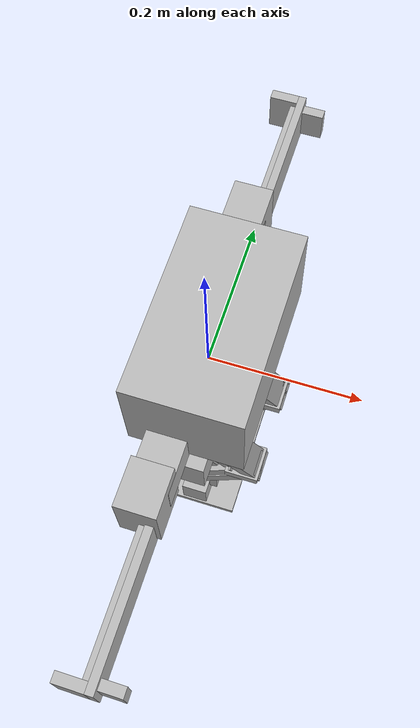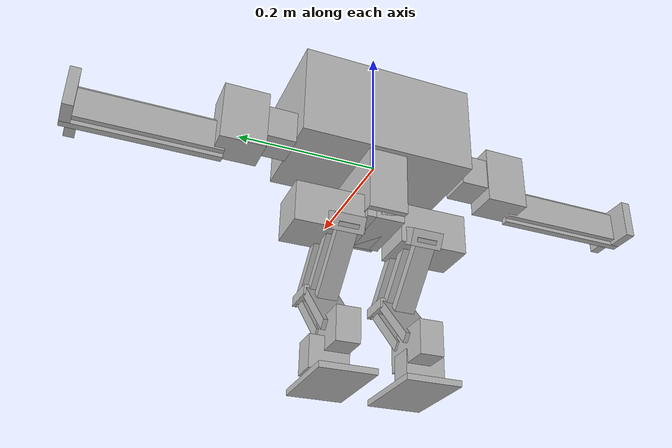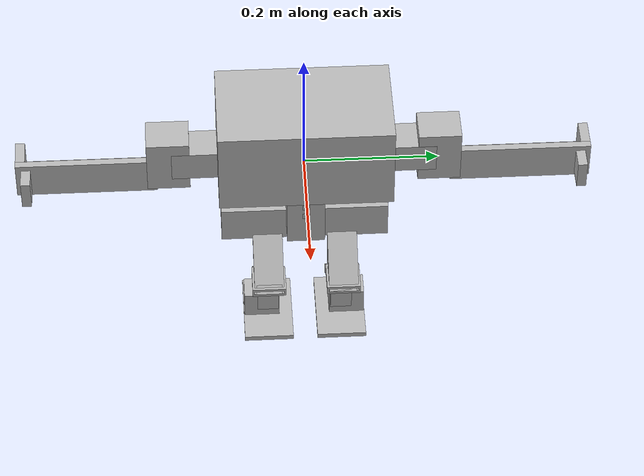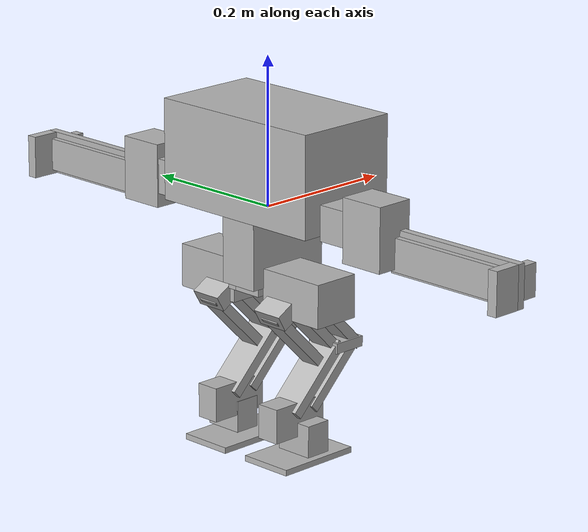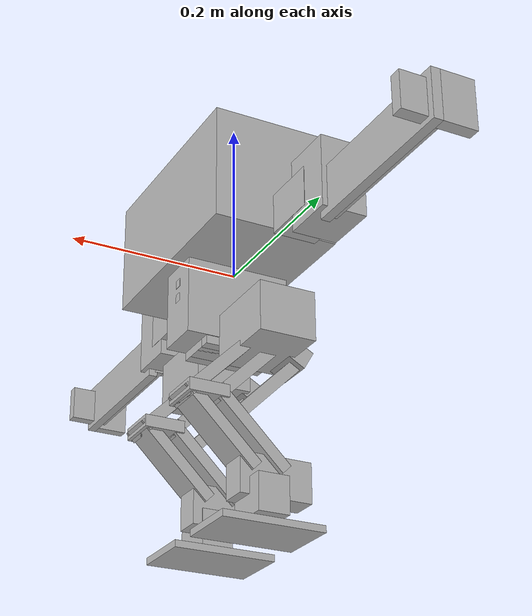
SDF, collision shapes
<?xml version='1.0' encoding='utf-8'?>
<sdf version="1.7">
  <model name="kuroko">
    <link name="body_link">
      <inertial>
        <pose>0.009948 0 -0.04774 0 -0 0</pose>
        <mass>0.398</mass>
        <inertia>
          <ixx>0.000417341</ixx>
          <ixy>0</ixy>
          <ixz>-1.33917e-05</ixz>
          <iyy>0.000855722</iyy>
          <iyz>0</iyz>
          <izz>0.000651176</izz>
        </inertia>
      </inertial>
      <collision name="body_link_fixed_joint_lump__waist_link_collision">
        <pose>0.0084 0 -0.0483 0 -0 0</pose>
        <geometry>
          <box>
            <size>0.1247 0.056 0.0965</size>
          </box>
        </geometry>
        <surface>
          <contact>
            <ode>
              <kp>1e+06</kp>
              <kd>100</kd>
              <max_vel>10</max_vel>
              <min_depth>0.0001</min_depth>
            </ode>
          </contact>
          <friction>
            <ode>
              <mu>0.1</mu>
            </ode>
          </friction>
        </surface>
        <max_contacts>6</max_contacts>
      </collision>
      <collision name="body_link_fixed_joint_lump__camera_base_link_collision_1">
        <pose>0.07 0 -0.026 0 -0 0</pose>
        <geometry>
          <box>
            <size>0.002 0.01 0.01</size>
          </box>
        </geometry>
      </collision>
      <visual name="body_link_fixed_joint_lump__waist_link_visual">
        <pose>0 0 0 0 -0 0</pose>
        <geometry>
          <mesh>
            <scale>1 1 1</scale>
            <uri>/home/nyx/lib/isaaclab/kuroko_ros/kuroko_description/meshes/kuroko/stl/waist.stl</uri>
          </mesh>
        </geometry>
      </visual>
      <visual name="body_link_fixed_joint_lump__camera_base_link_visual_1">
        <pose>0.07 0 -0.026 0 -0 0</pose>
        <geometry>
          <box>
            <size>0.002 0.01 0.01</size>
          </box>
        </geometry>
      </visual>
      <velocity_decay>
        <linear>0</linear>
        <angular>0</angular>
      </velocity_decay>
      <self_collide>0</self_collide>
      <sensor name="camera_camera_cam" type="camera">
        <camera name="camera">
          <horizontal_fov>2.2</horizontal_fov>
          <image>
            <width>384</width>
            <height>216</height>
            <format>B8G8R8</format>
          </image>
          <distortion>
            <k1>-0.011469</k1>
            <k2>-0.009562</k2>
            <p1>0.000937</p1>
            <p2>-0.001691</p2>
            <k3>0</k3>
          </distortion>
          <clip>
            <near>0.1</near>
            <far>100</far>
          </clip>
        </camera>
        <plugin name="camera_camera_plugin" filename="libgazebo_ros_camera.so">
          <alwaysOn>1</alwaysOn>
          <updateRate>30</updateRate>
          <cameraName>camera</cameraName>
          <imageTopicName>resized/image</imageTopicName>
          <cameraInfoTopicName>resized/camera_info</cameraInfoTopicName>
          <frameName>camera_optical_link</frameName>
          <hackBaseline>0</hackBaseline>
          <autoDistortion>1</autoDistortion>
          <borderCrop>1</borderCrop>
        </plugin>
        <pose>0.071 0 -0.026 0 -0 0</pose>
      </sensor>
    </link>
    <joint name="chest" type="revolute">
      <pose relative_to="body_link">0 0 0 0 -0 0</pose>
      <parent>body_link</parent>
      <child>chest_link</child>
      <axis>
        <xyz>0 0 1</xyz>
        <limit>
          <lower>-3.14</lower>
          <upper>3.14</upper>
          <effort>3.1</effort>
          <velocity>6.5</velocity>
        </limit>
        <dynamics>
          <damping>0.477</damping>
          <friction>0</friction>
          <spring_reference>0</spring_reference>
          <spring_stiffness>0</spring_stiffness>
        </dynamics>
      </axis>
      <physics>
        <ode>
          <implicit_spring_damper>1</implicit_spring_damper>
          <cfm_damping>1</cfm_damping>
          <limit>
            <cfm>0</cfm>
            <erp>0.2</erp>
          </limit>
        </ode>
      </physics>
    </joint>
    <link name="chest_link">
      <pose relative_to="chest">0 0 0 0 -0 0</pose>
      <inertial>
        <pose>0.012 0 0.0635 0 -0 0</pose>
        <mass>0.806</mass>
        <inertia>
          <ixx>0.00565147</ixx>
          <ixy>0</ixy>
          <ixz>0</ixz>
          <iyy>0.00272085</iyy>
          <iyz>0</iyz>
          <izz>0.00587305</izz>
        </inertia>
      </inertial>
      <collision name="chest_link_collision">
        <pose>0.012 0 0.0635 0 -0 0</pose>
        <geometry>
          <box>
            <size>0.148 0.256 0.1364</size>
          </box>
        </geometry>
        <surface>
          <contact>
            <ode>
              <kp>1e+06</kp>
              <kd>100</kd>
              <max_vel>10</max_vel>
              <min_depth>0.0001</min_depth>
            </ode>
          </contact>
          <friction>
            <ode>
              <mu>0.1</mu>
            </ode>
          </friction>
        </surface>
        <max_contacts>6</max_contacts>
      </collision>
      <visual name="chest_link_visual">
        <pose>0 0 0 0 -0 0</pose>
        <geometry>
          <mesh>
            <scale>1 1 1</scale>
            <uri>/home/nyx/lib/isaaclab/kuroko_ros/kuroko_description/meshes/kuroko/stl/chest.stl</uri>
          </mesh>
        </geometry>
      </visual>
      <velocity_decay>
        <linear>0</linear>
        <angular>0</angular>
      </velocity_decay>
      <self_collide>0</self_collide>
    </link>
    <joint name="shoulder_l_pitch" type="revolute">
      <pose relative_to="chest_link">0 0.128 0.01275 0 -0 0</pose>
      <parent>chest_link</parent>
      <child>shoulder_l_pitch_link</child>
      <axis>
        <xyz>0 1 0</xyz>
        <limit>
          <lower>-3.14</lower>
          <upper>3.14</upper>
          <effort>3.1</effort>
          <velocity>6.5</velocity>
        </limit>
        <dynamics>
          <damping>0.477</damping>
          <friction>0</friction>
          <spring_reference>0</spring_reference>
          <spring_stiffness>0</spring_stiffness>
        </dynamics>
      </axis>
      <physics>
        <ode>
          <implicit_spring_damper>1</implicit_spring_damper>
          <cfm_damping>1</cfm_damping>
          <limit>
            <cfm>0</cfm>
            <erp>0.2</erp>
          </limit>
        </ode>
      </physics>
    </joint>
    <link name="shoulder_l_pitch_link">
      <pose relative_to="shoulder_l_pitch">0 0 0 0 -0 0</pose>
      <inertial>
        <pose>-0.0096 0.034 0 0 -0 0</pose>
        <mass>0.165</mass>
        <inertia>
          <ixx>9.46034e-05</ixx>
          <ixy>0</ixy>
          <ixz>0</ixz>
          <iyy>6.72092e-05</iyy>
          <iyz>0</iyz>
          <izz>9.97657e-05</izz>
        </inertia>
      </inertial>
      <collision name="shoulder_l_pitch_link_collision">
        <pose>-0.0096 0.034 0 0 -0 0</pose>
        <geometry>
          <box>
            <size>0.0513 0.068 0.0475</size>
          </box>
        </geometry>
        <surface>
          <contact>
            <ode>
              <kp>1e+06</kp>
              <kd>100</kd>
              <max_vel>10</max_vel>
              <min_depth>0.0001</min_depth>
            </ode>
          </contact>
          <friction>
            <ode>
              <mu>0.01</mu>
            </ode>
          </friction>
        </surface>
        <max_contacts>6</max_contacts>
      </collision>
      <visual name="shoulder_l_pitch_link_visual">
        <pose>0 0 0 0 -0 0</pose>
        <geometry>
          <mesh>
            <scale>1 1 1</scale>
            <uri>/home/nyx/lib/isaaclab/kuroko_ros/kuroko_description/meshes/kuroko/stl/shoulder_l_pitch.stl</uri>
          </mesh>
        </geometry>
      </visual>
      <velocity_decay>
        <linear>0</linear>
        <angular>0</angular>
      </velocity_decay>
      <self_collide>0</self_collide>
    </link>
    <joint name="shoulder_l_roll" type="revolute">
      <pose relative_to="shoulder_l_pitch_link">0 0.05425 0 1.5708 -0 0</pose>
      <parent>shoulder_l_pitch_link</parent>
      <child>shoulder_l_roll_link</child>
      <axis>
        <xyz>1 0 0</xyz>
        <limit>
          <lower>-3.14</lower>
          <upper>3.14</upper>
          <effort>8.9</effort>
          <velocity>6.9</velocity>
        </limit>
        <dynamics>
          <damping>1.29</damping>
          <friction>0</friction>
          <spring_reference>0</spring_reference>
          <spring_stiffness>0</spring_stiffness>
        </dynamics>
      </axis>
      <physics>
        <ode>
          <implicit_spring_damper>1</implicit_spring_damper>
          <cfm_damping>1</cfm_damping>
          <limit>
            <cfm>0</cfm>
            <erp>0.2</erp>
          </limit>
        </ode>
      </physics>
    </joint>
    <link name="shoulder_l_roll_link">
      <pose relative_to="shoulder_l_roll">0 0 0 0 -0 0</pose>
      <inertial>
        <pose>-0.0108 0 -0.0186 0 -0 0</pose>
        <mass>0.183</mass>
        <inertia>
          <ixx>0.000173894</ixx>
          <ixy>0</ixy>
          <ixz>0</ixz>
          <iyy>0.000103942</iyy>
          <iyz>0</iyz>
          <izz>0.000155626</izz>
        </inertia>
      </inertial>
      <collision name="shoulder_l_roll_link_collision">
        <pose>-0.0108 0 -0.0186 0 -0 0</pose>
        <geometry>
          <box>
            <size>0.053 0.086 0.0633</size>
          </box>
        </geometry>
        <surface>
          <contact>
            <ode>
              <kp>1e+06</kp>
              <kd>100</kd>
              <max_vel>10</max_vel>
              <min_depth>0.0001</min_depth>
            </ode>
          </contact>
          <friction>
            <ode>
              <mu>0.01</mu>
            </ode>
          </friction>
        </surface>
        <max_contacts>6</max_contacts>
      </collision>
      <visual name="shoulder_l_roll_link_visual">
        <pose>0 0 0 0 -0 0</pose>
        <geometry>
          <mesh>
            <scale>1 1 1</scale>
            <uri>/home/nyx/lib/isaaclab/kuroko_ros/kuroko_description/meshes/kuroko/stl/shoulder_l_roll.stl</uri>
          </mesh>
        </geometry>
      </visual>
      <velocity_decay>
        <linear>0</linear>
        <angular>0</angular>
      </velocity_decay>
      <self_collide>0</self_collide>
    </link>
    <joint name="elbow_l_front" type="revolute">
      <pose relative_to="shoulder_l_roll_link">0 -0.023 -0.036 0 -0 0</pose>
      <parent>shoulder_l_roll_link</parent>
      <child>elbow_l_front_link</child>
      <axis>
        <xyz>-0 1 -0</xyz>
        <limit>
          <lower>-2.618</lower>
          <upper>2.618</upper>
          <effort>3.1</effort>
          <velocity>6.5</velocity>
        </limit>
        <dynamics>
          <damping>0.477</damping>
          <friction>0</friction>
          <spring_reference>0</spring_reference>
          <spring_stiffness>0</spring_stiffness>
        </dynamics>
      </axis>
      <physics>
        <ode>
          <implicit_spring_damper>1</implicit_spring_damper>
          <cfm_damping>1</cfm_damping>
          <limit>
            <cfm>0</cfm>
            <erp>0.2</erp>
          </limit>
        </ode>
      </physics>
    </joint>
    <link name="elbow_l_front_link">
      <pose relative_to="elbow_l_front">0 0 0 0 -0 0</pose>
      <inertial>
        <pose>0.0043 0 -0.104 0 -0 0</pose>
        <mass>0.032</mass>
        <inertia>
          <ixx>0.000124341</ixx>
          <ixy>0</ixy>
          <ixz>0</ixz>
          <iyy>0.000120533</iyy>
          <iyz>0</iyz>
          <izz>1.41333e-05</izz>
        </inertia>
      </inertial>
      <collision name="elbow_l_front_link_collision">
        <pose>0.0043 0 -0.104 0 -0 0</pose>
        <geometry>
          <box>
            <size>0.01085 0.058 0.208</size>
          </box>
        </geometry>
        <surface>
          <contact>
            <ode>
              <kp>1e+06</kp>
              <kd>100</kd>
              <max_vel>10</max_vel>
              <min_depth>0.0001</min_depth>
            </ode>
          </contact>
          <friction>
            <ode>
              <mu>0.01</mu>
            </ode>
          </friction>
        </surface>
        <max_contacts>6</max_contacts>
      </collision>
      <collision name="elbow_l_front_link_collision_1">
        <pose>-0.0206 0 -0.201 0 -0 0</pose>
        <geometry>
          <box>
            <size>0.039 0.058 0.014</size>
          </box>
        </geometry>
        <surface>
          <contact>
            <ode>
              <kp>1e+06</kp>
              <kd>100</kd>
              <max_vel>10</max_vel>
              <min_depth>0.0001</min_depth>
            </ode>
          </contact>
          <friction>
            <ode>
              <mu>0.01</mu>
            </ode>
          </friction>
        </surface>
        <max_contacts>6</max_contacts>
      </collision>
      <visual name="elbow_l_front_link_visual">
        <pose>0 0 0 0 -0 0</pose>
        <geometry>
          <mesh>
            <scale>1 1 1</scale>
            <uri>/home/nyx/lib/isaaclab/kuroko_ros/kuroko_description/meshes/kuroko/stl/elbow_l_front.stl</uri>
          </mesh>
        </geometry>
      </visual>
      <velocity_decay>
        <linear>0</linear>
        <angular>0</angular>
      </velocity_decay>
      <self_collide>0</self_collide>
    </link>
    <joint name="elbow_l_rear" type="revolute">
      <pose relative_to="shoulder_l_roll_link">0 -0.024 -0.036 0 -0 0</pose>
      <parent>shoulder_l_roll_link</parent>
      <child>elbow_l_rear_link</child>
      <axis>
        <xyz>0 1 0</xyz>
        <limit>
          <lower>-2.618</lower>
          <upper>2.618</upper>
          <effort>3.1</effort>
          <velocity>6.5</velocity>
        </limit>
        <dynamics>
          <damping>0.477</damping>
          <friction>0</friction>
          <spring_reference>0</spring_reference>
          <spring_stiffness>0</spring_stiffness>
        </dynamics>
      </axis>
      <physics>
        <ode>
          <implicit_spring_damper>1</implicit_spring_damper>
          <cfm_damping>1</cfm_damping>
          <limit>
            <cfm>0</cfm>
            <erp>0.2</erp>
          </limit>
        </ode>
      </physics>
    </joint>
    <link name="elbow_l_rear_link">
      <pose relative_to="elbow_l_rear">0 0 0 0 -0 0</pose>
      <inertial>
        <pose>-0.0043 0 -0.1 0 -0 0</pose>
        <mass>0.031</mass>
        <inertia>
          <ixx>0.000108335</ixx>
          <ixy>0</ixy>
          <ixz>0</ixz>
          <iyy>0.000108335</iyy>
          <iyz>0</iyz>
          <izz>1.00027e-05</izz>
        </inertia>
      </inertial>
      <collision name="elbow_l_rear_link_collision">
        <pose>-0.0043 0 -0.1 0 -0 0</pose>
        <geometry>
          <box>
            <size>0.01085 0.044 0.2</size>
          </box>
        </geometry>
        <surface>
          <contact>
            <ode>
              <kp>1e+06</kp>
              <kd>100</kd>
              <max_vel>10</max_vel>
              <min_depth>0.0001</min_depth>
            </ode>
          </contact>
          <friction>
            <ode>
              <mu>0.01</mu>
            </ode>
          </friction>
        </surface>
        <max_contacts>6</max_contacts>
      </collision>
      <collision name="elbow_l_rear_link_collision_1">
        <pose>0.0206 0 -0.193 0 -0 0</pose>
        <geometry>
          <box>
            <size>0.039 0.044 0.014</size>
          </box>
        </geometry>
        <surface>
          <contact>
            <ode>
              <kp>1e+06</kp>
              <kd>100</kd>
              <max_vel>10</max_vel>
              <min_depth>0.0001</min_depth>
            </ode>
          </contact>
          <friction>
            <ode>
              <mu>0.01</mu>
            </ode>
          </friction>
        </surface>
        <max_contacts>6</max_contacts>
      </collision>
      <visual name="elbow_l_rear_link_visual">
        <pose>0 0 0 0 -0 0</pose>
        <geometry>
          <mesh>
            <scale>1 1 1</scale>
            <uri>/home/nyx/lib/isaaclab/kuroko_ros/kuroko_description/meshes/kuroko/stl/elbow_l_rear.stl</uri>
          </mesh>
        </geometry>
      </visual>
      <velocity_decay>
        <linear>0</linear>
        <angular>0</angular>
      </velocity_decay>
      <self_collide>0</self_collide>
    </link>
    <joint name="shoulder_r_pitch" type="revolute">
      <pose relative_to="chest_link">0 -0.128 0.01275 0 -0 0</pose>
      <parent>chest_link</parent>
      <child>shoulder_r_pitch_link</child>
      <axis>
        <xyz>-0 1 -0</xyz>
        <limit>
          <lower>-3.14</lower>
          <upper>3.14</upper>
          <effort>3.1</effort>
          <velocity>6.5</velocity>
        </limit>
        <dynamics>
          <damping>0.477</damping>
          <friction>0</friction>
          <spring_reference>0</spring_reference>
          <spring_stiffness>0</spring_stiffness>
        </dynamics>
      </axis>
      <physics>
        <ode>
          <implicit_spring_damper>1</implicit_spring_damper>
          <cfm_damping>1</cfm_damping>
          <limit>
            <cfm>0</cfm>
            <erp>0.2</erp>
          </limit>
        </ode>
      </physics>
    </joint>
    <link name="shoulder_r_pitch_link">
      <pose relative_to="shoulder_r_pitch">0 0 0 0 -0 0</pose>
      <inertial>
        <pose>-0.0096 -0.034 0 0 -0 0</pose>
        <mass>0.165</mass>
        <inertia>
          <ixx>9.46034e-05</ixx>
          <ixy>0</ixy>
          <ixz>0</ixz>
          <iyy>6.72092e-05</iyy>
          <iyz>0</iyz>
          <izz>9.97657e-05</izz>
        </inertia>
      </inertial>
      <collision name="shoulder_r_pitch_link_collision">
        <pose>-0.0096 -0.034 0 0 -0 0</pose>
        <geometry>
          <box>
            <size>0.0513 0.068 0.0475</size>
          </box>
        </geometry>
        <surface>
          <contact>
            <ode>
              <kp>1e+06</kp>
              <kd>100</kd>
              <max_vel>10</max_vel>
              <min_depth>0.0001</min_depth>
            </ode>
          </contact>
          <friction>
            <ode>
              <mu>0.01</mu>
            </ode>
          </friction>
        </surface>
        <max_contacts>6</max_contacts>
      </collision>
      <visual name="shoulder_r_pitch_link_visual">
        <pose>0 0 0 0 -0 0</pose>
        <geometry>
          <mesh>
            <scale>1 1 1</scale>
            <uri>/home/nyx/lib/isaaclab/kuroko_ros/kuroko_description/meshes/kuroko/stl/shoulder_r_pitch.stl</uri>
          </mesh>
        </geometry>
      </visual>
      <velocity_decay>
        <linear>0</linear>
        <angular>0</angular>
      </velocity_decay>
      <self_collide>0</self_collide>
    </link>
    <joint name="shoulder_r_roll" type="revolute">
      <pose relative_to="shoulder_r_pitch_link">0 -0.05425 0 -1.5708 0 0</pose>
      <parent>shoulder_r_pitch_link</parent>
      <child>shoulder_r_roll_link</child>
      <axis>
        <xyz>1 0 0</xyz>
        <limit>
          <lower>-3.14</lower>
          <upper>3.14</upper>
          <effort>8.9</effort>
          <velocity>6.9</velocity>
        </limit>
        <dynamics>
          <damping>1.29</damping>
          <friction>0</friction>
          <spring_reference>0</spring_reference>
          <spring_stiffness>0</spring_stiffness>
        </dynamics>
      </axis>
      <physics>
        <ode>
          <implicit_spring_damper>1</implicit_spring_damper>
          <cfm_damping>1</cfm_damping>
          <limit>
            <cfm>0</cfm>
            <erp>0.2</erp>
          </limit>
        </ode>
      </physics>
    </joint>
    <link name="shoulder_r_roll_link">
      <pose relative_to="shoulder_r_roll">0 0 0 0 -0 0</pose>
      <inertial>
        <pose>-0.0108 0 -0.0186 0 -0 0</pose>
        <mass>0.183</mass>
        <inertia>
          <ixx>0.000173894</ixx>
          <ixy>0</ixy>
          <ixz>0</ixz>
          <iyy>0.000103942</iyy>
          <iyz>0</iyz>
          <izz>0.000155626</izz>
        </inertia>
      </inertial>
      <collision name="shoulder_r_roll_link_collision">
        <pose>-0.0108 0 -0.0186 0 -0 0</pose>
        <geometry>
          <box>
            <size>0.053 0.086 0.0633</size>
          </box>
        </geometry>
        <surface>
          <contact>
            <ode>
              <kp>1e+06</kp>
              <kd>100</kd>
              <max_vel>10</max_vel>
              <min_depth>0.0001</min_depth>
            </ode>
          </contact>
          <friction>
            <ode>
              <mu>0.01</mu>
            </ode>
          </friction>
        </surface>
        <max_contacts>6</max_contacts>
      </collision>
      <visual name="shoulder_r_roll_link_visual">
        <pose>0 0 0 0 -0 0</pose>
        <geometry>
          <mesh>
            <scale>1 1 1</scale>
            <uri>/home/nyx/lib/isaaclab/kuroko_ros/kuroko_description/meshes/kuroko/stl/shoulder_r_roll.stl</uri>
          </mesh>
        </geometry>
      </visual>
      <velocity_decay>
        <linear>0</linear>
        <angular>0</angular>
      </velocity_decay>
      <self_collide>0</self_collide>
    </link>
    <joint name="elbow_r_front" type="revolute">
      <pose relative_to="shoulder_r_roll_link">0 0.023 -0.036 0 -0 0</pose>
      <parent>shoulder_r_roll_link</parent>
      <child>elbow_r_front_link</child>
      <axis>
        <xyz>0 1 0</xyz>
        <limit>
          <lower>-2.618</lower>
          <upper>2.618</upper>
          <effort>3.1</effort>
          <velocity>6.5</velocity>
        </limit>
        <dynamics>
          <damping>0.477</damping>
          <friction>0</friction>
          <spring_reference>0</spring_reference>
          <spring_stiffness>0</spring_stiffness>
        </dynamics>
      </axis>
      <physics>
        <ode>
          <implicit_spring_damper>1</implicit_spring_damper>
          <cfm_damping>1</cfm_damping>
          <limit>
            <cfm>0</cfm>
            <erp>0.2</erp>
          </limit>
        </ode>
      </physics>
    </joint>
    <link name="elbow_r_front_link">
      <pose relative_to="elbow_r_front">0 0 0 0 -0 0</pose>
      <inertial>
        <pose>0.0043 0 -0.104 0 -0 0</pose>
        <mass>0.032</mass>
        <inertia>
          <ixx>0.000124341</ixx>
          <ixy>0</ixy>
          <ixz>0</ixz>
          <iyy>0.000120533</iyy>
          <iyz>0</iyz>
          <izz>1.41333e-05</izz>
        </inertia>
      </inertial>
      <collision name="elbow_r_front_link_collision">
        <pose>0.0043 0 -0.104 0 -0 0</pose>
        <geometry>
          <box>
            <size>0.01085 0.058 0.208</size>
          </box>
        </geometry>
        <surface>
          <contact>
            <ode>
              <kp>1e+06</kp>
              <kd>100</kd>
              <max_vel>10</max_vel>
              <min_depth>0.0001</min_depth>
            </ode>
          </contact>
          <friction>
            <ode>
              <mu>0.01</mu>
            </ode>
          </friction>
        </surface>
        <max_contacts>6</max_contacts>
      </collision>
      <collision name="elbow_r_front_link_collision_1">
        <pose>-0.0206 0 -0.201 0 -0 0</pose>
        <geometry>
          <box>
            <size>0.039 0.058 0.014</size>
          </box>
        </geometry>
        <surface>
          <contact>
            <ode>
              <kp>1e+06</kp>
              <kd>100</kd>
              <max_vel>10</max_vel>
              <min_depth>0.0001</min_depth>
            </ode>
          </contact>
          <friction>
            <ode>
              <mu>0.01</mu>
            </ode>
          </friction>
        </surface>
        <max_contacts>6</max_contacts>
      </collision>
      <visual name="elbow_r_front_link_visual">
        <pose>0 0 0 0 -0 0</pose>
        <geometry>
          <mesh>
            <scale>1 1 1</scale>
            <uri>/home/nyx/lib/isaaclab/kuroko_ros/kuroko_description/meshes/kuroko/stl/elbow_r_front.stl</uri>
          </mesh>
        </geometry>
      </visual>
      <velocity_decay>
        <linear>0</linear>
        <angular>0</angular>
      </velocity_decay>
      <self_collide>0</self_collide>
    </link>
    <joint name="elbow_r_rear" type="revolute">
      <pose relative_to="shoulder_r_roll_link">0 0.024 -0.036 0 -0 0</pose>
      <parent>shoulder_r_roll_link</parent>
      <child>elbow_r_rear_link</child>
      <axis>
        <xyz>-0 1 -0</xyz>
        <limit>
          <lower>-2.618</lower>
          <upper>2.618</upper>
          <effort>3.1</effort>
          <velocity>6.5</velocity>
        </limit>
        <dynamics>
          <damping>0.477</damping>
          <friction>0</friction>
          <spring_reference>0</spring_reference>
          <spring_stiffness>0</spring_stiffness>
        </dynamics>
      </axis>
      <physics>
        <ode>
          <implicit_spring_damper>1</implicit_spring_damper>
          <cfm_damping>1</cfm_damping>
          <limit>
            <cfm>0</cfm>
            <erp>0.2</erp>
          </limit>
        </ode>
      </physics>
    </joint>
    <link name="elbow_r_rear_link">
      <pose relative_to="elbow_r_rear">0 0 0 0 -0 0</pose>
      <inertial>
        <pose>-0.0043 0 -0.1 0 -0 0</pose>
        <mass>0.031</mass>
        <inertia>
          <ixx>0.000108335</ixx>
          <ixy>0</ixy>
          <ixz>0</ixz>
          <iyy>0.000108335</iyy>
          <iyz>0</iyz>
          <izz>1.00027e-05</izz>
        </inertia>
      </inertial>
      <collision name="elbow_r_rear_link_collision">
        <pose>-0.0043 0 -0.1 0 -0 0</pose>
        <geometry>
          <box>
            <size>0.01085 0.044 0.2</size>
          </box>
        </geometry>
        <surface>
          <contact>
            <ode>
              <kp>1e+06</kp>
              <kd>100</kd>
              <max_vel>10</max_vel>
              <min_depth>0.0001</min_depth>
            </ode>
          </contact>
          <friction>
            <ode>
              <mu>0.01</mu>
            </ode>
          </friction>
        </surface>
        <max_contacts>6</max_contacts>
      </collision>
      <collision name="elbow_r_rear_link_collision_1">
        <pose>0.0206 0 -0.193 0 -0 0</pose>
        <geometry>
          <box>
            <size>0.039 0.044 0.014</size>
          </box>
        </geometry>
        <surface>
          <contact>
            <ode>
              <kp>1e+06</kp>
              <kd>100</kd>
              <max_vel>10</max_vel>
              <min_depth>0.0001</min_depth>
            </ode>
          </contact>
          <friction>
            <ode>
              <mu>0.01</mu>
            </ode>
          </friction>
        </surface>
        <max_contacts>6</max_contacts>
      </collision>
      <visual name="elbow_r_rear_link_visual">
        <pose>0 0 0 0 -0 0</pose>
        <geometry>
          <mesh>
            <scale>1 1 1</scale>
            <uri>/home/nyx/lib/isaaclab/kuroko_ros/kuroko_description/meshes/kuroko/stl/elbow_r_rear.stl</uri>
          </mesh>
        </geometry>
      </visual>
      <velocity_decay>
        <linear>0</linear>
        <angular>0</angular>
      </velocity_decay>
      <self_collide>0</self_collide>
    </link>
    <joint name="hip_l_roll" type="revolute">
      <pose relative_to="body_link">0 0 -0.08425 0 -0 0</pose>
      <parent>body_link</parent>
      <child>hip_l_roll_link</child>
      <axis>
        <xyz>1 -0 -0</xyz>
        <limit>
          <lower>-1.864</lower>
          <upper>0.555</upper>
          <effort>3.1</effort>
          <velocity>6.5</velocity>
        </limit>
        <dynamics>
          <damping>0.477</damping>
          <friction>0</friction>
          <spring_reference>0</spring_reference>
          <spring_stiffness>0</spring_stiffness>
        </dynamics>
      </axis>
      <physics>
        <ode>
          <implicit_spring_damper>1</implicit_spring_damper>
          <cfm_damping>1</cfm_damping>
          <limit>
            <cfm>0</cfm>
            <erp>0.2</erp>
          </limit>
        </ode>
      </physics>
    </joint>
    <link name="hip_l_roll_link">
      <pose relative_to="hip_l_roll">0 0 0 0 -0 0</pose>
      <inertial>
        <pose>0.00125 0.0065 -0.004125 0 -0 0</pose>
        <mass>0.026</mass>
        <inertia>
          <ixx>1e-05</ixx>
          <ixy>0</ixy>
          <ixz>0</ixz>
          <iyy>2.11858e-05</iyy>
          <iyz>0</iyz>
          <izz>2.19808e-05</izz>
        </inertia>
      </inertial>
      <collision name="hip_l_roll_link_collision">
        <pose>0.00125 0.0065 -0.004125 0 -0 0</pose>
        <geometry>
          <box>
            <size>0.092 0.041 0.03625</size>
          </box>
        </geometry>
        <surface>
          <contact>
            <ode>
              <kp>1e+06</kp>
              <kd>100</kd>
              <max_vel>10</max_vel>
              <min_depth>0.0001</min_depth>
            </ode>
          </contact>
          <friction>
            <ode>
              <mu>0.01</mu>
            </ode>
          </friction>
        </surface>
        <max_contacts>6</max_contacts>
      </collision>
      <visual name="hip_l_roll_link_visual">
        <pose>0 0 0 0 -0 0</pose>
        <geometry>
          <mesh>
            <scale>1 1 1</scale>
            <uri>/home/nyx/lib/isaaclab/kuroko_ros/kuroko_description/meshes/kuroko/stl/hip_l_roll.stl</uri>
          </mesh>
        </geometry>
      </visual>
      <velocity_decay>
        <linear>0</linear>
        <angular>0</angular>
      </velocity_decay>
      <self_collide>0</self_collide>
    </link>
    <joint name="hip_l_pitch" type="revolute">
      <pose relative_to="hip_l_roll_link">0 0.027 0 0 -0 0</pose>
      <parent>hip_l_roll_link</parent>
      <child>hip_l_pitch_link</child>
      <axis>
        <xyz>0 1 0</xyz>
        <limit>
          <lower>-3.14</lower>
          <upper>3.14</upper>
          <effort>3.1</effort>
          <velocity>6.5</velocity>
        </limit>
        <dynamics>
          <damping>0.477</damping>
          <friction>0</friction>
          <spring_reference>0</spring_reference>
          <spring_stiffness>0</spring_stiffness>
        </dynamics>
      </axis>
      <physics>
        <ode>
          <implicit_spring_damper>1</implicit_spring_damper>
          <cfm_damping>1</cfm_damping>
          <limit>
            <cfm>0</cfm>
            <erp>0.2</erp>
          </limit>
        </ode>
      </physics>
    </joint>
    <link name="hip_l_pitch_link">
      <pose relative_to="hip_l_pitch">0 0 0 0 -0 0</pose>
      <inertial>
        <pose>-0.00175 0.049 -0.015 0 -0 0</pose>
        <mass>0.478</mass>
        <inertia>
          <ixx>0.000518879</ixx>
          <ixy>0</ixy>
          <ixz>0</ixz>
          <iyy>0.000315131</iyy>
          <iyz>0</iyz>
          <izz>0.000561371</izz>
        </inertia>
      </inertial>
      <collision name="hip_l_pitch_link_collision">
        <pose>-0.00175 0.049 -0.015 0 -0 0</pose>
        <geometry>
          <box>
            <size>0.067 0.098 0.0585</size>
          </box>
        </geometry>
        <surface>
          <contact>
            <ode>
              <kp>1e+06</kp>
              <kd>100</kd>
              <max_vel>10</max_vel>
              <min_depth>0.0001</min_depth>
            </ode>
          </contact>
          <friction>
            <ode>
              <mu>0.01</mu>
            </ode>
          </friction>
        </surface>
        <max_contacts>6</max_contacts>
      </collision>
      <visual name="hip_l_pitch_link_visual">
        <pose>0 0 0 0 -0 0</pose>
        <geometry>
          <mesh>
            <scale>1 1 1</scale>
            <uri>/home/nyx/lib/isaaclab/kuroko_ros/kuroko_description/meshes/kuroko/stl/hip_l_pitch.stl</uri>
          </mesh>
        </geometry>
      </visual>
      <velocity_decay>
        <linear>0</linear>
        <angular>0</angular>
      </velocity_decay>
      <self_collide>0</self_collide>
    </link>
    <joint name="shin_l_active" type="revolute">
      <pose relative_to="hip_l_pitch_link">-0.0185 0.02925 -0.0305 0 1.0472 0</pose>
      <parent>hip_l_pitch_link</parent>
      <child>shin_l_active_link</child>
      <axis>
        <xyz>-0 1 -0</xyz>
        <limit>
          <lower>-1.8588</lower>
          <upper>0.4974</upper>
          <effort>8.9</effort>
          <velocity>6.9</velocity>
        </limit>
        <dynamics>
          <damping>1.29</damping>
          <friction>0</friction>
          <spring_reference>0</spring_reference>
          <spring_stiffness>0</spring_stiffness>
        </dynamics>
      </axis>
      <physics>
        <ode>
          <implicit_spring_damper>1</implicit_spring_damper>
          <cfm_damping>1</cfm_damping>
          <limit>
            <cfm>0</cfm>
            <erp>0.2</erp>
          </limit>
        </ode>
      </physics>
    </joint>
    <link name="shin_l_active_link">
      <pose relative_to="shin_l_active">0 0 0 0 -0 0</pose>
      <inertial>
        <pose>-0.004745 0 -0.015 0 -0 0</pose>
        <mass>0.008</mass>
        <inertia>
          <ixx>1e-05</ixx>
          <ixy>0</ixy>
          <ixz>0</ixz>
          <iyy>1e-05</iyy>
          <iyz>0</iyz>
          <izz>1e-05</izz>
        </inertia>
      </inertial>
      <collision name="shin_l_active_link_collision">
        <pose>-0.004745 0 -0.015 0 -0 0</pose>
        <geometry>
          <box>
            <size>0.02349 0.0445 0.044</size>
          </box>
        </geometry>
        <surface>
          <contact>
            <ode>
              <kp>1e+06</kp>
              <kd>100</kd>
              <max_vel>10</max_vel>
              <min_depth>0.0001</min_depth>
            </ode>
          </contact>
          <friction>
            <ode>
              <mu>0.01</mu>
            </ode>
          </friction>
        </surface>
        <max_contacts>6</max_contacts>
      </collision>
      <visual name="shin_l_active_link_visual">
        <pose>0 0 0 0 -0 0</pose>
        <geometry>
          <mesh>
            <scale>1 1 1</scale>
            <uri>/home/nyx/lib/isaaclab/kuroko_ros/kuroko_description/meshes/kuroko/stl/shin_l_active.stl</uri>
          </mesh>
        </geometry>
      </visual>
      <velocity_decay>
        <linear>0</linear>
        <angular>0</angular>
      </velocity_decay>
      <self_collide>0</self_collide>
    </link>
    <joint name="thigh_l_active" type="revolute">
      <pose relative_to="hip_l_pitch_link">0.015 0.02925 -0.0305 0 -0.785398 0</pose>
      <parent>hip_l_pitch_link</parent>
      <child>thigh_l_active_link</child>
      <axis>
        <xyz>-0 1 -0</xyz>
        <limit>
          <lower>-0.4974</lower>
          <upper>1.8588</upper>
          <effort>8.9</effort>
          <velocity>6.9</velocity>
        </limit>
        <dynamics>
          <damping>1.29</damping>
          <friction>0</friction>
          <spring_reference>0</spring_reference>
          <spring_stiffness>0</spring_stiffness>
        </dynamics>
      </axis>
      <physics>
        <ode>
          <implicit_spring_damper>1</implicit_spring_damper>
          <cfm_damping>1</cfm_damping>
          <limit>
            <cfm>0</cfm>
            <erp>0.2</erp>
          </limit>
        </ode>
      </physics>
    </joint>
    <link name="thigh_l_active_link">
      <pose relative_to="thigh_l_active">0 0 0 0 -0 0</pose>
      <inertial>
        <pose>0 0 -0.05 0 -0 0</pose>
        <mass>0.012</mass>
        <inertia>
          <ixx>1.49763e-05</ixx>
          <ixy>0</ixy>
          <ixz>0</ixz>
          <iyy>1.3192e-05</iyy>
          <iyz>0</iyz>
          <izz>1e-05</izz>
        </inertia>
      </inertial>
      <collision name="thigh_l_active_link_collision">
        <pose>0 0 -0.05 0 -0 0</pose>
        <geometry>
          <box>
            <size>0.014 0.0445 0.114</size>
          </box>
        </geometry>
        <surface>
          <contact>
            <ode>
              <kp>1e+06</kp>
              <kd>100</kd>
              <max_vel>10</max_vel>
              <min_depth>0.0001</min_depth>
            </ode>
          </contact>
          <friction>
            <ode>
              <mu>0</mu>
            </ode>
          </friction>
        </surface>
        <max_contacts>6</max_contacts>
      </collision>
      <visual name="thigh_l_active_link_visual">
        <pose>0 0 0 0 -0 0</pose>
        <geometry>
          <mesh>
            <scale>1 1 1</scale>
            <uri>/home/nyx/lib/isaaclab/kuroko_ros/kuroko_description/meshes/kuroko/stl/thigh_l_active.stl</uri>
          </mesh>
        </geometry>
      </visual>
      <velocity_decay>
        <linear>0</linear>
        <angular>0</angular>
      </velocity_decay>
      <self_collide>0</self_collide>
    </link>
    <joint name="shin_l_front_passive" type="revolute">
      <pose relative_to="thigh_l_active_link">0 0 -0.1 0 1.5708 0</pose>
      <parent>thigh_l_active_link</parent>
      <child>shin_l_front_passive_link</child>
      <axis>
        <xyz>0 1 0</xyz>
        <limit>
          <lower>-1.5708</lower>
          <upper>0.9948</upper>
          <effort>0</effort>
          <velocity>1000</velocity>
        </limit>
        <dynamics>
          <damping>0</damping>
          <friction>0</friction>
          <spring_reference>0</spring_reference>
          <spring_stiffness>0</spring_stiffness>
        </dynamics>
      </axis>
      <physics>
        <ode>
          <limit>
            <cfm>0</cfm>
            <erp>0.2</erp>
          </limit>
        </ode>
      </physics>
      <physics>
        <ode>
          <implicit_spring_damper>1</implicit_spring_damper>
          <cfm_damping>0</cfm_damping>
          <cfm>1e-07</cfm>
          <erp>0.8</erp>
          <limit>
            <cfm>1e-07</cfm>
            <erp>0.8</erp>
          </limit>
        </ode>
      </physics>
    </joint>
    <link name="shin_l_front_passive_link">
      <pose relative_to="shin_l_front_passive">0 0 0 0 -0 0</pose>
      <inertial>
        <pose>0 0 -0.05 0 -0 0</pose>
        <mass>0.013</mass>
        <inertia>
          <ixx>1.56848e-05</ixx>
          <ixy>0</ixy>
          <ixz>0</ixz>
          <iyy>1.42913e-05</iyy>
          <iyz>0</iyz>
          <izz>1e-05</izz>
        </inertia>
      </inertial>
      <collision name="shin_l_front_passive_link_collision">
        <pose>0 0 -0.05 0 -0 0</pose>
        <geometry>
          <box>
            <size>0.014 0.0385 0.114</size>
          </box>
        </geometry>
        <surface>
          <contact>
            <ode>
              <kp>1e+06</kp>
              <kd>100</kd>
              <max_vel>10</max_vel>
              <min_depth>0.0001</min_depth>
            </ode>
          </contact>
          <friction>
            <ode>
              <mu>0</mu>
            </ode>
          </friction>
        </surface>
        <max_contacts>6</max_contacts>
      </collision>
      <visual name="shin_l_front_passive_link_visual">
        <pose>0 0 0 0 -0 0</pose>
        <geometry>
          <mesh>
            <scale>1 1 1</scale>
            <uri>/home/nyx/lib/isaaclab/kuroko_ros/kuroko_description/meshes/kuroko/stl/shin_r_front_passive.stl</uri>
          </mesh>
        </geometry>
      </visual>
      <velocity_decay>
        <linear>0</linear>
        <angular>0</angular>
      </velocity_decay>
      <self_collide>0</self_collide>
    </link>
    <joint name="thigh_l_middle_passive" type="revolute">
      <pose relative_to="hip_l_pitch_link">-0.0185 0.02925 -0.0305 0 -0.785398 0</pose>
      <parent>hip_l_pitch_link</parent>
      <child>thigh_l_middle_passive_link</child>
      <axis>
        <xyz>0 1 0</xyz>
        <limit>
          <lower>-0.4974</lower>
          <upper>1.8588</upper>
          <effort>0</effort>
          <velocity>1000</velocity>
        </limit>
        <dynamics>
          <damping>0</damping>
          <friction>0</friction>
          <spring_reference>0</spring_reference>
          <spring_stiffness>0</spring_stiffness>
        </dynamics>
      </axis>
      <physics>
        <ode>
          <limit>
            <cfm>0</cfm>
            <erp>0.2</erp>
          </limit>
        </ode>
      </physics>
      <physics>
        <ode>
          <implicit_spring_damper>1</implicit_spring_damper>
          <cfm_damping>0</cfm_damping>
          <cfm>1e-07</cfm>
          <erp>0.8</erp>
          <limit>
            <cfm>1e-07</cfm>
            <erp>0.8</erp>
          </limit>
        </ode>
      </physics>
    </joint>
    <link name="thigh_l_middle_passive_link">
      <pose relative_to="thigh_l_middle_passive">0 0 0 0 -0 0</pose>
      <inertial>
        <pose>0 0 -0.05 0 -0 0</pose>
        <mass>0.012</mass>
        <inertia>
          <ixx>1.41862e-05</ixx>
          <ixy>0</ixy>
          <ixz>0</ixz>
          <iyy>1.3192e-05</iyy>
          <iyz>0</iyz>
          <izz>1e-05</izz>
        </inertia>
      </inertial>
      <collision name="thigh_l_middle_passive_link_collision">
        <pose>0 0 -0.05 0 -0 0</pose>
        <geometry>
          <box>
            <size>0.014 0.0345 0.114</size>
          </box>
        </geometry>
        <surface>
          <contact>
            <ode>
              <kp>1e+06</kp>
              <kd>100</kd>
              <max_vel>10</max_vel>
              <min_depth>0.0001</min_depth>
            </ode>
          </contact>
          <friction>
            <ode>
              <mu>0</mu>
            </ode>
          </friction>
        </surface>
        <max_contacts>6</max_contacts>
      </collision>
      <visual name="thigh_l_middle_passive_link_visual">
        <pose>0 0 0 0 -0 0</pose>
        <geometry>
          <mesh>
            <scale>1 1 1</scale>
            <uri>/home/nyx/lib/isaaclab/kuroko_ros/kuroko_description/meshes/kuroko/stl/thigh_r_middle_passive.stl</uri>
          </mesh>
        </geometry>
      </visual>
      <velocity_decay>
        <linear>0</linear>
        <angular>0</angular>
      </velocity_decay>
      <self_collide>0</self_collide>
    </link>
    <joint name="shin_l_rear_passive" type="revolute">
      <pose relative_to="thigh_l_middle_passive_link">0 0 -0.1 0 1.5708 0</pose>
      <parent>thigh_l_middle_passive_link</parent>
      <child>shin_l_rear_passive_link</child>
      <axis>
        <xyz>0 1 0</xyz>
        <limit>
          <lower>-1.5708</lower>
          <upper>0.9948</upper>
          <effort>0</effort>
          <velocity>1000</velocity>
        </limit>
        <dynamics>
          <damping>0</damping>
          <friction>0</friction>
          <spring_reference>0</spring_reference>
          <spring_stiffness>0</spring_stiffness>
        </dynamics>
      </axis>
      <physics>
        <ode>
          <limit>
            <cfm>0</cfm>
            <erp>0.2</erp>
          </limit>
        </ode>
      </physics>
      <physics>
        <ode>
          <implicit_spring_damper>1</implicit_spring_damper>
          <cfm_damping>0</cfm_damping>
          <cfm>1e-07</cfm>
          <erp>0.8</erp>
          <limit>
            <cfm>1e-07</cfm>
            <erp>0.8</erp>
          </limit>
        </ode>
      </physics>
    </joint>
    <link name="shin_l_rear_passive_link">
      <pose relative_to="shin_l_rear_passive">0 0 0 0 -0 0</pose>
      <inertial>
        <pose>0 0 -0.05 0 -0 0</pose>
        <mass>0.016</mass>
        <inertia>
          <ixx>1.99683e-05</ixx>
          <ixy>0</ixy>
          <ixz>0</ixz>
          <iyy>1.75893e-05</iyy>
          <iyz>0</iyz>
          <izz>1e-05</izz>
        </inertia>
      </inertial>
      <collision name="shin_l_rear_passive_link_collision">
        <pose>0 0 -0.05 0 -0 0</pose>
        <geometry>
          <box>
            <size>0.014 0.0445 0.114</size>
          </box>
        </geometry>
        <surface>
          <contact>
            <ode>
              <kp>1e+06</kp>
              <kd>100</kd>
              <max_vel>10</max_vel>
              <min_depth>0.0001</min_depth>
            </ode>
          </contact>
          <friction>
            <ode>
              <mu>0</mu>
            </ode>
          </friction>
        </surface>
        <max_contacts>6</max_contacts>
      </collision>
      <visual name="shin_l_rear_passive_link_visual">
        <pose>0 0 0 0 -0 0</pose>
        <geometry>
          <mesh>
            <scale>1 1 1</scale>
            <uri>/home/nyx/lib/isaaclab/kuroko_ros/kuroko_description/meshes/kuroko/stl/shin_r_rear_passive.stl</uri>
          </mesh>
        </geometry>
      </visual>
      <velocity_decay>
        <linear>0</linear>
        <angular>0</angular>
      </velocity_decay>
      <self_collide>0</self_collide>
    </link>
    <joint name="ankle_l_rear_passive" type="revolute">
      <pose relative_to="shin_l_rear_passive_link">0 0 -0.1 0 -0.785398 0</pose>
      <parent>shin_l_rear_passive_link</parent>
      <child>ankle_l_rear_passive_link</child>
      <axis>
        <xyz>0 1 0</xyz>
        <limit>
          <lower>-0.4974</lower>
          <upper>1.8588</upper>
          <effort>0</effort>
          <velocity>1000</velocity>
        </limit>
        <dynamics>
          <damping>0</damping>
          <friction>0</friction>
          <spring_reference>0</spring_reference>
          <spring_stiffness>0</spring_stiffness>
        </dynamics>
      </axis>
    </joint>
    <link name="ankle_l_rear_passive_link">
      <pose relative_to="ankle_l_rear_passive">0 0 0 0 -0 0</pose>
      <inertial>
        <pose>0.005 0 -0.013 0 -0 0</pose>
        <mass>0.104</mass>
        <inertia>
          <ixx>2.78937e-05</ixx>
          <ixy>0</ixy>
          <ixz>0</ixz>
          <iyy>8.2095e-05</iyy>
          <iyz>0</iyz>
          <izz>7.25097e-05</izz>
        </inertia>
      </inertial>
      <collision name="ankle_l_rear_passive_link_collision">
        <pose>0.005 0 -0.013 0 -0 0</pose>
        <geometry>
          <box>
            <size>0.0855 0.0325 0.0465</size>
          </box>
        </geometry>
      </collision>
      <visual name="ankle_l_rear_passive_link_visual">
        <pose>0.0335 0 0 0 -0 0</pose>
        <geometry>
          <mesh>
            <scale>1 1 1</scale>
            <uri>/home/nyx/lib/isaaclab/kuroko_ros/kuroko_description/meshes/kuroko/stl/ankle_r_pitch_passive.stl</uri>
          </mesh>
        </geometry>
      </visual>
    </link>
    <joint name="ankle_l_roll" type="revolute">
      <pose relative_to="ankle_l_rear_passive_link">0.0185 0 -0.027 0 -0 0</pose>
      <parent>ankle_l_rear_passive_link</parent>
      <child>ankle_l_roll_link</child>
      <axis>
        <xyz>1 0 0</xyz>
        <limit>
          <lower>-1.5708</lower>
          <upper>0.3704</upper>
          <effort>3.1</effort>
          <velocity>6.5</velocity>
        </limit>
        <dynamics>
          <damping>0.477</damping>
          <friction>0</friction>
          <spring_reference>0</spring_reference>
          <spring_stiffness>0</spring_stiffness>
        </dynamics>
      </axis>
      <physics>
        <ode>
          <implicit_spring_damper>1</implicit_spring_damper>
          <cfm_damping>1</cfm_damping>
          <limit>
            <cfm>0</cfm>
            <erp>0.2</erp>
          </limit>
        </ode>
      </physics>
    </joint>
    <link name="ankle_l_roll_link">
      <pose relative_to="ankle_l_roll">0 0 0 0 -0 0</pose>
      <inertial>
        <pose>0 0.009375 -0.01175 0 -0 0</pose>
        <mass>0.136</mass>
        <inertia>
          <ixx>5.3698e-05</ixx>
          <ixy>0</ixy>
          <ixz>0</ixz>
          <iyy>3.60542e-05</iyy>
          <iyz>0</iyz>
          <izz>4.78415e-05</izz>
        </inertia>
      </inertial>
      <collision name="ankle_l_roll_link_collision">
        <pose>0 0.009375 -0.01175 0 -0 0</pose>
        <geometry>
          <box>
            <size>0.0365 0.05375 0.043</size>
          </box>
        </geometry>
        <surface>
          <contact>
            <ode>
              <kp>1e+06</kp>
              <kd>100</kd>
              <max_vel>10</max_vel>
              <min_depth>0.0001</min_depth>
            </ode>
          </contact>
          <friction>
            <ode>
              <mu>0</mu>
            </ode>
          </friction>
        </surface>
        <max_contacts>6</max_contacts>
      </collision>
      <visual name="ankle_l_roll_link_visual">
        <pose>0 0 0 0 -0 0</pose>
        <geometry>
          <mesh>
            <scale>1 1 1</scale>
            <uri>/home/nyx/lib/isaaclab/kuroko_ros/kuroko_description/meshes/kuroko/stl/ankle_l_roll.stl</uri>
          </mesh>
        </geometry>
      </visual>
      <velocity_decay>
        <linear>0</linear>
        <angular>0</angular>
      </velocity_decay>
      <self_collide>0</self_collide>
    </link>
    <joint name="ankle_l_yaw" type="revolute">
      <pose relative_to="ankle_l_roll_link">0 0 -0.03825 0 -0 0</pose>
      <parent>ankle_l_roll_link</parent>
      <child>ankle_l_yaw_link</child>
      <axis>
        <xyz>-0 -0 1</xyz>
        <limit>
          <lower>-3.1416</lower>
          <upper>3.1416</upper>
          <effort>3.1</effort>
          <velocity>6.5</velocity>
        </limit>
        <dynamics>
          <damping>0.477</damping>
          <friction>0</friction>
          <spring_reference>0</spring_reference>
          <spring_stiffness>0</spring_stiffness>
        </dynamics>
      </axis>
      <physics>
        <ode>
          <implicit_spring_damper>1</implicit_spring_damper>
          <cfm_damping>1</cfm_damping>
          <limit>
            <cfm>0</cfm>
            <erp>0.2</erp>
          </limit>
        </ode>
      </physics>
    </joint>
    <link name="ankle_l_yaw_link">
      <pose relative_to="ankle_l_yaw">0 0 0 0 -0 0</pose>
      <inertial>
        <pose>0 0 -0.004 0 -0 0</pose>
        <mass>0.043</mass>
        <inertia>
          <ixx>2.03856e-05</ixx>
          <ixy>0</ixy>
          <ixz>0</ixz>
          <iyy>5.18293e-05</iyy>
          <iyz>0</iyz>
          <izz>7.17562e-05</izz>
        </inertia>
      </inertial>
      <collision name="ankle_l_yaw_link_collision">
        <pose>0 0 -0.004 0 -0 0</pose>
        <geometry>
          <box>
            <size>0.12 0.075 0.008</size>
          </box>
        </geometry>
        <surface>
          <contact>
            <ode>
              <kp>2e+06</kp>
              <kd>200</kd>
              <max_vel>1</max_vel>
              <min_depth>0.0001</min_depth>
            </ode>
          </contact>
          <friction>
            <ode>
              <mu>1</mu>
            </ode>
          </friction>
        </surface>
        <max_contacts>10</max_contacts>
      </collision>
      <visual name="ankle_l_yaw_link_visual">
        <pose>0 0 0 0 -0 0</pose>
        <geometry>
          <mesh>
            <scale>1 1 1</scale>
            <uri>/home/nyx/lib/isaaclab/kuroko_ros/kuroko_description/meshes/kuroko/stl/ankle_r_yaw.stl</uri>
          </mesh>
        </geometry>
      </visual>
      <velocity_decay>
        <linear>0</linear>
        <angular>0</angular>
      </velocity_decay>
      <self_collide>0</self_collide>
    </link>
    <joint name="knee_l_rear_passive" type="revolute">
      <pose relative_to="shin_l_rear_passive_link">0 0 0 0 -0.785398 0</pose>
      <parent>shin_l_rear_passive_link</parent>
      <child>knee_l_passive_link</child>
      <axis>
        <xyz>0 1 0</xyz>
        <limit>
          <lower>-3.14159</lower>
          <upper>3.14159</upper>
          <effort>0</effort>
          <velocity>1000</velocity>
        </limit>
        <dynamics>
          <damping>0</damping>
          <friction>0</friction>
          <spring_reference>0</spring_reference>
          <spring_stiffness>0</spring_stiffness>
        </dynamics>
      </axis>
    </joint>
    <link name="knee_l_passive_link">
      <pose relative_to="knee_l_rear_passive">0 0 0 0 -0 0</pose>
      <inertial>
        <pose>0.01675 0 0 0 -0 0</pose>
        <mass>0.007</mass>
        <inertia>
          <ixx>1e-05</ixx>
          <ixy>0</ixy>
          <ixz>0</ixz>
          <iyy>1e-05</iyy>
          <iyz>0</iyz>
          <izz>1e-05</izz>
        </inertia>
      </inertial>
      <collision name="knee_l_passive_link_collision">
        <pose>0.01675 0 0 0 -0 0</pose>
        <geometry>
          <box>
            <size>0.0475 0.0505 0.014</size>
          </box>
        </geometry>
        <surface>
          <contact>
            <ode>
              <kp>1e+06</kp>
              <kd>100</kd>
              <max_vel>10</max_vel>
              <min_depth>0.0001</min_depth>
            </ode>
          </contact>
          <friction>
            <ode>
              <mu>0.01</mu>
            </ode>
          </friction>
        </surface>
        <max_contacts>6</max_contacts>
      </collision>
      <visual name="knee_l_passive_link_visual">
        <pose>0.0335 0 0 0 -0 0</pose>
        <geometry>
          <mesh>
            <scale>1 1 1</scale>
            <uri>/home/nyx/lib/isaaclab/kuroko_ros/kuroko_description/meshes/kuroko/stl/knee_r_passive.stl</uri>
          </mesh>
        </geometry>
      </visual>
      <velocity_decay>
        <linear>0</linear>
        <angular>0</angular>
      </velocity_decay>
      <self_collide>0</self_collide>
    </link>
    <joint name="thigh_l_rear_passive" type="revolute">
      <pose relative_to="shin_l_rear_passive_link">-0.007765 0 -0.028978 0 -1.5708 0</pose>
      <parent>shin_l_rear_passive_link</parent>
      <child>thigh_l_rear_passive_link</child>
      <axis>
        <xyz>0 1 0</xyz>
        <limit>
          <lower>-0.9948</lower>
          <upper>1.5708</upper>
          <effort>0</effort>
          <velocity>1000</velocity>
        </limit>
        <dynamics>
          <damping>0</damping>
          <friction>0</friction>
          <spring_reference>0</spring_reference>
          <spring_stiffness>0</spring_stiffness>
        </dynamics>
      </axis>
      <physics>
        <ode>
          <limit>
            <cfm>0</cfm>
            <erp>0.2</erp>
          </limit>
        </ode>
      </physics>
      <physics>
        <ode>
          <implicit_spring_damper>1</implicit_spring_damper>
          <cfm_damping>0</cfm_damping>
          <cfm>1e-07</cfm>
          <erp>0.8</erp>
          <limit>
            <cfm>1e-07</cfm>
            <erp>0.8</erp>
          </limit>
        </ode>
      </physics>
    </joint>
    <link name="thigh_l_rear_passive_link">
      <pose relative_to="thigh_l_rear_passive">0 0 0 0 -0 0</pose>
      <inertial>
        <pose>0 0 0.05 0 -0 0</pose>
        <mass>0.011</mass>
        <inertia>
          <ixx>1.26576e-05</ixx>
          <ixy>0</ixy>
          <ixz>0</ixz>
          <iyy>1.20927e-05</iyy>
          <iyz>0</iyz>
          <izz>1e-05</izz>
        </inertia>
      </inertial>
      <collision name="thigh_l_rear_passive_link_collision">
        <pose>0 0 0.05 0 -0 0</pose>
        <geometry>
          <box>
            <size>0.014 0.0285 0.114</size>
          </box>
        </geometry>
        <surface>
          <contact>
            <ode>
              <kp>1e+06</kp>
              <kd>100</kd>
              <max_vel>10</max_vel>
              <min_depth>0.0001</min_depth>
            </ode>
          </contact>
          <friction>
            <ode>
              <mu>0</mu>
            </ode>
          </friction>
        </surface>
        <max_contacts>6</max_contacts>
      </collision>
      <visual name="thigh_l_rear_passive_link_visual">
        <pose>0 0 0.1 0 -0 0</pose>
        <geometry>
          <mesh>
            <scale>1 1 1</scale>
            <uri>/home/nyx/lib/isaaclab/kuroko_ros/kuroko_description/meshes/kuroko/stl/thigh_r_rear_passive.stl</uri>
          </mesh>
        </geometry>
      </visual>
      <velocity_decay>
        <linear>0</linear>
        <angular>0</angular>
      </velocity_decay>
      <self_collide>0</self_collide>
    </link>
    <joint name="hip_r_roll" type="revolute">
      <pose relative_to="body_link">0 0 -0.08425 0 -0 0</pose>
      <parent>body_link</parent>
      <child>hip_r_roll_link</child>
      <axis>
        <xyz>1 0 0</xyz>
        <limit>
          <lower>-0.555</lower>
          <upper>1.864</upper>
          <effort>3.1</effort>
          <velocity>6.5</velocity>
        </limit>
        <dynamics>
          <damping>0.477</damping>
          <friction>0</friction>
          <spring_reference>0</spring_reference>
          <spring_stiffness>0</spring_stiffness>
        </dynamics>
      </axis>
      <physics>
        <ode>
          <implicit_spring_damper>1</implicit_spring_damper>
          <cfm_damping>1</cfm_damping>
          <limit>
            <cfm>0</cfm>
            <erp>0.2</erp>
          </limit>
        </ode>
      </physics>
    </joint>
    <link name="hip_r_roll_link">
      <pose relative_to="hip_r_roll">0 0 0 0 -0 0</pose>
      <inertial>
        <pose>0.00125 -0.0065 -0.004125 0 -0 0</pose>
        <mass>0.026</mass>
        <inertia>
          <ixx>1e-05</ixx>
          <ixy>0</ixy>
          <ixz>0</ixz>
          <iyy>2.11858e-05</iyy>
          <iyz>0</iyz>
          <izz>2.19808e-05</izz>
        </inertia>
      </inertial>
      <collision name="hip_r_roll_link_collision">
        <pose>0.00125 -0.0065 -0.004125 0 -0 0</pose>
        <geometry>
          <box>
            <size>0.092 0.041 0.03625</size>
          </box>
        </geometry>
        <surface>
          <contact>
            <ode>
              <kp>1e+06</kp>
              <kd>100</kd>
              <max_vel>10</max_vel>
              <min_depth>0.0001</min_depth>
            </ode>
          </contact>
          <friction>
            <ode>
              <mu>0.01</mu>
            </ode>
          </friction>
        </surface>
        <max_contacts>6</max_contacts>
      </collision>
      <visual name="hip_r_roll_link_visual">
        <pose>0 0 0 0 -0 0</pose>
        <geometry>
          <mesh>
            <scale>1 1 1</scale>
            <uri>/home/nyx/lib/isaaclab/kuroko_ros/kuroko_description/meshes/kuroko/stl/hip_r_roll.stl</uri>
          </mesh>
        </geometry>
      </visual>
      <velocity_decay>
        <linear>0</linear>
        <angular>0</angular>
      </velocity_decay>
      <self_collide>0</self_collide>
    </link>
    <joint name="hip_r_pitch" type="revolute">
      <pose relative_to="hip_r_roll_link">0 -0.027 0 0 -0 0</pose>
      <parent>hip_r_roll_link</parent>
      <child>hip_r_pitch_link</child>
      <axis>
        <xyz>-0 1 -0</xyz>
        <limit>
          <lower>-3.1</lower>
          <upper>3.1</upper>
          <effort>3.1</effort>
          <velocity>6.5</velocity>
        </limit>
        <dynamics>
          <damping>0.477</damping>
          <friction>0</friction>
          <spring_reference>0</spring_reference>
          <spring_stiffness>0</spring_stiffness>
        </dynamics>
      </axis>
      <physics>
        <ode>
          <implicit_spring_damper>1</implicit_spring_damper>
          <cfm_damping>1</cfm_damping>
          <limit>
            <cfm>0</cfm>
            <erp>0.2</erp>
          </limit>
        </ode>
      </physics>
    </joint>
    <link name="hip_r_pitch_link">
      <pose relative_to="hip_r_pitch">0 0 0 0 -0 0</pose>
      <inertial>
        <pose>-0.00175 -0.049 -0.015 0 -0 0</pose>
        <mass>0.478</mass>
        <inertia>
          <ixx>0.000518879</ixx>
          <ixy>0</ixy>
          <ixz>0</ixz>
          <iyy>0.000315131</iyy>
          <iyz>0</iyz>
          <izz>0.000561371</izz>
        </inertia>
      </inertial>
      <collision name="hip_r_pitch_link_collision">
        <pose>-0.00175 -0.049 -0.015 0 -0 0</pose>
        <geometry>
          <box>
            <size>0.067 0.098 0.0585</size>
          </box>
        </geometry>
        <surface>
          <contact>
            <ode>
              <kp>1e+06</kp>
              <kd>100</kd>
              <max_vel>10</max_vel>
              <min_depth>0.0001</min_depth>
            </ode>
          </contact>
          <friction>
            <ode>
              <mu>0.01</mu>
            </ode>
          </friction>
        </surface>
        <max_contacts>6</max_contacts>
      </collision>
      <visual name="hip_r_pitch_link_visual">
        <pose>0 0 0 0 -0 0</pose>
        <geometry>
          <mesh>
            <scale>1 1 1</scale>
            <uri>/home/nyx/lib/isaaclab/kuroko_ros/kuroko_description/meshes/kuroko/stl/hip_r_pitch.stl</uri>
          </mesh>
        </geometry>
      </visual>
      <velocity_decay>
        <linear>0</linear>
        <angular>0</angular>
      </velocity_decay>
      <self_collide>0</self_collide>
    </link>
    <joint name="shin_r_active" type="revolute">
      <pose relative_to="hip_r_pitch_link">-0.0185 -0.02925 -0.0305 0 1.0472 0</pose>
      <parent>hip_r_pitch_link</parent>
      <child>shin_r_active_link</child>
      <axis>
        <xyz>0 1 0</xyz>
        <limit>
          <lower>-1.8588</lower>
          <upper>0.4974</upper>
          <effort>8.9</effort>
          <velocity>6.9</velocity>
        </limit>
        <dynamics>
          <damping>1.29</damping>
          <friction>0</friction>
          <spring_reference>0</spring_reference>
          <spring_stiffness>0</spring_stiffness>
        </dynamics>
      </axis>
      <physics>
        <ode>
          <implicit_spring_damper>1</implicit_spring_damper>
          <cfm_damping>1</cfm_damping>
          <limit>
            <cfm>0</cfm>
            <erp>0.2</erp>
          </limit>
        </ode>
      </physics>
    </joint>
    <link name="shin_r_active_link">
      <pose relative_to="shin_r_active">0 0 0 0 -0 0</pose>
      <inertial>
        <pose>-0.004745 0 -0.015 0 -0 0</pose>
        <mass>0.008</mass>
        <inertia>
          <ixx>1e-05</ixx>
          <ixy>0</ixy>
          <ixz>0</ixz>
          <iyy>1e-05</iyy>
          <iyz>0</iyz>
          <izz>1e-05</izz>
        </inertia>
      </inertial>
      <collision name="shin_r_active_link_collision">
        <pose>-0.004745 0 -0.015 0 -0 0</pose>
        <geometry>
          <box>
            <size>0.02349 0.0445 0.044</size>
          </box>
        </geometry>
        <surface>
          <contact>
            <ode>
              <kp>1e+06</kp>
              <kd>100</kd>
              <max_vel>10</max_vel>
              <min_depth>0.0001</min_depth>
            </ode>
          </contact>
          <friction>
            <ode>
              <mu>0.01</mu>
            </ode>
          </friction>
        </surface>
        <max_contacts>6</max_contacts>
      </collision>
      <visual name="shin_r_active_link_visual">
        <pose>0 0 0 0 -0 0</pose>
        <geometry>
          <mesh>
            <scale>1 1 1</scale>
            <uri>/home/nyx/lib/isaaclab/kuroko_ros/kuroko_description/meshes/kuroko/stl/shin_r_active.stl</uri>
          </mesh>
        </geometry>
      </visual>
      <velocity_decay>
        <linear>0</linear>
        <angular>0</angular>
      </velocity_decay>
      <self_collide>0</self_collide>
    </link>
    <joint name="thigh_r_active" type="revolute">
      <pose relative_to="hip_r_pitch_link">0.015 -0.02925 -0.0305 0 -0.785398 0</pose>
      <parent>hip_r_pitch_link</parent>
      <child>thigh_r_active_link</child>
      <axis>
        <xyz>0 1 0</xyz>
        <limit>
          <lower>-0.4974</lower>
          <upper>1.8588</upper>
          <effort>8.9</effort>
          <velocity>6.9</velocity>
        </limit>
        <dynamics>
          <damping>1.29</damping>
          <friction>0</friction>
          <spring_reference>0</spring_reference>
          <spring_stiffness>0</spring_stiffness>
        </dynamics>
      </axis>
      <physics>
        <ode>
          <implicit_spring_damper>1</implicit_spring_damper>
          <cfm_damping>1</cfm_damping>
          <limit>
            <cfm>0</cfm>
            <erp>0.2</erp>
          </limit>
        </ode>
      </physics>
    </joint>
    <link name="thigh_r_active_link">
      <pose relative_to="thigh_r_active">0 0 0 0 -0 0</pose>
      <inertial>
        <pose>0 0 -0.05 0 -0 0</pose>
        <mass>0.012</mass>
        <inertia>
          <ixx>1.49763e-05</ixx>
          <ixy>0</ixy>
          <ixz>0</ixz>
          <iyy>1.3192e-05</iyy>
          <iyz>0</iyz>
          <izz>1e-05</izz>
        </inertia>
      </inertial>
      <collision name="thigh_r_active_link_collision">
        <pose>0 0 -0.05 0 -0 0</pose>
        <geometry>
          <box>
            <size>0.014 0.0445 0.114</size>
          </box>
        </geometry>
        <surface>
          <contact>
            <ode>
              <kp>1e+06</kp>
              <kd>100</kd>
              <max_vel>10</max_vel>
              <min_depth>0.0001</min_depth>
            </ode>
          </contact>
          <friction>
            <ode>
              <mu>0</mu>
            </ode>
          </friction>
        </surface>
        <max_contacts>6</max_contacts>
      </collision>
      <visual name="thigh_r_active_link_visual">
        <pose>0 0 0 0 -0 0</pose>
        <geometry>
          <mesh>
            <scale>1 1 1</scale>
            <uri>/home/nyx/lib/isaaclab/kuroko_ros/kuroko_description/meshes/kuroko/stl/thigh_r_active.stl</uri>
          </mesh>
        </geometry>
      </visual>
      <velocity_decay>
        <linear>0</linear>
        <angular>0</angular>
      </velocity_decay>
      <self_collide>0</self_collide>
    </link>
    <joint name="shin_r_front_passive" type="revolute">
      <pose relative_to="thigh_r_active_link">0 0 -0.1 0 1.5708 0</pose>
      <parent>thigh_r_active_link</parent>
      <child>shin_r_front_passive_link</child>
      <axis>
        <xyz>0 1 0</xyz>
        <limit>
          <lower>-1.5708</lower>
          <upper>0.9948</upper>
          <effort>0</effort>
          <velocity>1000</velocity>
        </limit>
        <dynamics>
          <damping>0</damping>
          <friction>0</friction>
          <spring_reference>0</spring_reference>
          <spring_stiffness>0</spring_stiffness>
        </dynamics>
      </axis>
      <physics>
        <ode>
          <limit>
            <cfm>0</cfm>
            <erp>0.2</erp>
          </limit>
        </ode>
      </physics>
      <physics>
        <ode>
          <implicit_spring_damper>1</implicit_spring_damper>
          <cfm_damping>0</cfm_damping>
          <cfm>1e-07</cfm>
          <erp>0.8</erp>
          <limit>
            <cfm>1e-07</cfm>
            <erp>0.8</erp>
          </limit>
        </ode>
      </physics>
    </joint>
    <link name="shin_r_front_passive_link">
      <pose relative_to="shin_r_front_passive">0 0 0 0 -0 0</pose>
      <inertial>
        <pose>0 0 -0.05 0 -0 0</pose>
        <mass>0.013</mass>
        <inertia>
          <ixx>1.56848e-05</ixx>
          <ixy>0</ixy>
          <ixz>0</ixz>
          <iyy>1.42913e-05</iyy>
          <iyz>0</iyz>
          <izz>1e-05</izz>
        </inertia>
      </inertial>
      <collision name="shin_r_front_passive_link_collision">
        <pose>0 0 -0.05 0 -0 0</pose>
        <geometry>
          <box>
            <size>0.014 0.0385 0.114</size>
          </box>
        </geometry>
        <surface>
          <contact>
            <ode>
              <kp>1e+06</kp>
              <kd>100</kd>
              <max_vel>10</max_vel>
              <min_depth>0.0001</min_depth>
            </ode>
          </contact>
          <friction>
            <ode>
              <mu>0</mu>
            </ode>
          </friction>
        </surface>
        <max_contacts>6</max_contacts>
      </collision>
      <visual name="shin_r_front_passive_link_visual">
        <pose>0 0 0 0 -0 0</pose>
        <geometry>
          <mesh>
            <scale>1 1 1</scale>
            <uri>/home/nyx/lib/isaaclab/kuroko_ros/kuroko_description/meshes/kuroko/stl/shin_r_front_passive.stl</uri>
          </mesh>
        </geometry>
      </visual>
      <velocity_decay>
        <linear>0</linear>
        <angular>0</angular>
      </velocity_decay>
      <self_collide>0</self_collide>
    </link>
    <joint name="thigh_r_middle_passive" type="revolute">
      <pose relative_to="hip_r_pitch_link">-0.0185 -0.02925 -0.0305 0 -0.785398 0</pose>
      <parent>hip_r_pitch_link</parent>
      <child>thigh_r_middle_passive_link</child>
      <axis>
        <xyz>0 1 0</xyz>
        <limit>
          <lower>-0.4974</lower>
          <upper>1.8588</upper>
          <effort>0</effort>
          <velocity>1000</velocity>
        </limit>
        <dynamics>
          <damping>0</damping>
          <friction>0</friction>
          <spring_reference>0</spring_reference>
          <spring_stiffness>0</spring_stiffness>
        </dynamics>
      </axis>
      <physics>
        <ode>
          <limit>
            <cfm>0</cfm>
            <erp>0.2</erp>
          </limit>
        </ode>
      </physics>
      <physics>
        <ode>
          <implicit_spring_damper>1</implicit_spring_damper>
          <cfm_damping>0</cfm_damping>
          <cfm>1e-07</cfm>
          <erp>0.8</erp>
          <limit>
            <cfm>1e-07</cfm>
            <erp>0.8</erp>
          </limit>
        </ode>
      </physics>
    </joint>
    <link name="thigh_r_middle_passive_link">
      <pose relative_to="thigh_r_middle_passive">0 0 0 0 -0 0</pose>
      <inertial>
        <pose>0 0 -0.05 0 -0 0</pose>
        <mass>0.012</mass>
        <inertia>
          <ixx>1.41862e-05</ixx>
          <ixy>0</ixy>
          <ixz>0</ixz>
          <iyy>1.3192e-05</iyy>
          <iyz>0</iyz>
          <izz>1e-05</izz>
        </inertia>
      </inertial>
      <collision name="thigh_r_middle_passive_link_collision">
        <pose>0 0 -0.05 0 -0 0</pose>
        <geometry>
          <box>
            <size>0.014 0.0345 0.114</size>
          </box>
        </geometry>
        <surface>
          <contact>
            <ode>
              <kp>1e+06</kp>
              <kd>100</kd>
              <max_vel>10</max_vel>
              <min_depth>0.0001</min_depth>
            </ode>
          </contact>
          <friction>
            <ode>
              <mu>0</mu>
            </ode>
          </friction>
        </surface>
        <max_contacts>6</max_contacts>
      </collision>
      <visual name="thigh_r_middle_passive_link_visual">
        <pose>0 0 0 0 -0 0</pose>
        <geometry>
          <mesh>
            <scale>1 1 1</scale>
            <uri>/home/nyx/lib/isaaclab/kuroko_ros/kuroko_description/meshes/kuroko/stl/thigh_r_middle_passive.stl</uri>
          </mesh>
        </geometry>
      </visual>
      <velocity_decay>
        <linear>0</linear>
        <angular>0</angular>
      </velocity_decay>
      <self_collide>0</self_collide>
    </link>
    <joint name="shin_r_rear_passive" type="revolute">
      <pose relative_to="thigh_r_middle_passive_link">0 0 -0.1 0 1.5708 0</pose>
      <parent>thigh_r_middle_passive_link</parent>
      <child>shin_r_rear_passive_link</child>
      <axis>
        <xyz>0 1 0</xyz>
        <limit>
          <lower>-1.5708</lower>
          <upper>0.9948</upper>
          <effort>0</effort>
          <velocity>1000</velocity>
        </limit>
        <dynamics>
          <damping>0</damping>
          <friction>0</friction>
          <spring_reference>0</spring_reference>
          <spring_stiffness>0</spring_stiffness>
        </dynamics>
      </axis>
      <physics>
        <ode>
          <limit>
            <cfm>0</cfm>
            <erp>0.2</erp>
          </limit>
        </ode>
      </physics>
      <physics>
        <ode>
          <implicit_spring_damper>1</implicit_spring_damper>
          <cfm_damping>0</cfm_damping>
          <cfm>1e-07</cfm>
          <erp>0.8</erp>
          <limit>
            <cfm>1e-07</cfm>
            <erp>0.8</erp>
          </limit>
        </ode>
      </physics>
    </joint>
    <link name="shin_r_rear_passive_link">
      <pose relative_to="shin_r_rear_passive">0 0 0 0 -0 0</pose>
      <inertial>
        <pose>0 0 -0.05 0 -0 0</pose>
        <mass>0.016</mass>
        <inertia>
          <ixx>1.99683e-05</ixx>
          <ixy>0</ixy>
          <ixz>0</ixz>
          <iyy>1.75893e-05</iyy>
          <iyz>0</iyz>
          <izz>1e-05</izz>
        </inertia>
      </inertial>
      <collision name="shin_r_rear_passive_link_collision">
        <pose>0 0 -0.05 0 -0 0</pose>
        <geometry>
          <box>
            <size>0.014 0.0445 0.114</size>
          </box>
        </geometry>
        <surface>
          <contact>
            <ode>
              <kp>1e+06</kp>
              <kd>100</kd>
              <max_vel>10</max_vel>
              <min_depth>0.0001</min_depth>
            </ode>
          </contact>
          <friction>
            <ode>
              <mu>0</mu>
            </ode>
          </friction>
        </surface>
        <max_contacts>6</max_contacts>
      </collision>
      <visual name="shin_r_rear_passive_link_visual">
        <pose>0 0 0 0 -0 0</pose>
        <geometry>
          <mesh>
            <scale>1 1 1</scale>
            <uri>/home/nyx/lib/isaaclab/kuroko_ros/kuroko_description/meshes/kuroko/stl/shin_r_rear_passive.stl</uri>
          </mesh>
        </geometry>
      </visual>
      <velocity_decay>
        <linear>0</linear>
        <angular>0</angular>
      </velocity_decay>
      <self_collide>0</self_collide>
    </link>
    <joint name="ankle_r_rear_passive" type="revolute">
      <pose relative_to="shin_r_rear_passive_link">0 0 -0.1 0 -0.785398 0</pose>
      <parent>shin_r_rear_passive_link</parent>
      <child>ankle_r_rear_passive_link</child>
      <axis>
        <xyz>0 1 0</xyz>
        <limit>
          <lower>-0.4974</lower>
          <upper>1.8588</upper>
          <effort>0</effort>
          <velocity>1000</velocity>
        </limit>
        <dynamics>
          <damping>0</damping>
          <friction>0</friction>
          <spring_reference>0</spring_reference>
          <spring_stiffness>0</spring_stiffness>
        </dynamics>
      </axis>
    </joint>
    <link name="ankle_r_rear_passive_link">
      <pose relative_to="ankle_r_rear_passive">0 0 0 0 -0 0</pose>
      <inertial>
        <pose>0.005 0 -0.013 0 -0 0</pose>
        <mass>0.104</mass>
        <inertia>
          <ixx>2.78937e-05</ixx>
          <ixy>0</ixy>
          <ixz>0</ixz>
          <iyy>8.2095e-05</iyy>
          <iyz>0</iyz>
          <izz>7.25097e-05</izz>
        </inertia>
      </inertial>
      <collision name="ankle_r_rear_passive_link_collision">
        <pose>0.005 0 -0.013 0 -0 0</pose>
        <geometry>
          <box>
            <size>0.0855 0.0325 0.0465</size>
          </box>
        </geometry>
      </collision>
      <visual name="ankle_r_rear_passive_link_visual">
        <pose>0.0335 0 0 0 -0 0</pose>
        <geometry>
          <mesh>
            <scale>1 1 1</scale>
            <uri>/home/nyx/lib/isaaclab/kuroko_ros/kuroko_description/meshes/kuroko/stl/ankle_r_pitch_passive.stl</uri>
          </mesh>
        </geometry>
      </visual>
    </link>
    <joint name="ankle_r_roll" type="revolute">
      <pose relative_to="ankle_r_rear_passive_link">0.0185 0 -0.027 0 -0 0</pose>
      <parent>ankle_r_rear_passive_link</parent>
      <child>ankle_r_roll_link</child>
      <axis>
        <xyz>1 0 0</xyz>
        <limit>
          <lower>-0.3704</lower>
          <upper>1.5708</upper>
          <effort>3.1</effort>
          <velocity>6.5</velocity>
        </limit>
        <dynamics>
          <damping>0.477</damping>
          <friction>0</friction>
          <spring_reference>0</spring_reference>
          <spring_stiffness>0</spring_stiffness>
        </dynamics>
      </axis>
      <physics>
        <ode>
          <implicit_spring_damper>1</implicit_spring_damper>
          <cfm_damping>1</cfm_damping>
          <limit>
            <cfm>0</cfm>
            <erp>0.2</erp>
          </limit>
        </ode>
      </physics>
    </joint>
    <link name="ankle_r_roll_link">
      <pose relative_to="ankle_r_roll">0 0 0 0 -0 0</pose>
      <inertial>
        <pose>0 -0.009375 -0.01175 0 -0 0</pose>
        <mass>0.136</mass>
        <inertia>
          <ixx>5.3698e-05</ixx>
          <ixy>0</ixy>
          <ixz>0</ixz>
          <iyy>3.60542e-05</iyy>
          <iyz>0</iyz>
          <izz>4.78415e-05</izz>
        </inertia>
      </inertial>
      <collision name="ankle_r_roll_link_collision">
        <pose>0 -0.009375 -0.01175 0 -0 0</pose>
        <geometry>
          <box>
            <size>0.0365 0.05375 0.043</size>
          </box>
        </geometry>
        <surface>
          <contact>
            <ode>
              <kp>1e+06</kp>
              <kd>100</kd>
              <max_vel>10</max_vel>
              <min_depth>0.0001</min_depth>
            </ode>
          </contact>
          <friction>
            <ode>
              <mu>0</mu>
            </ode>
          </friction>
        </surface>
        <max_contacts>6</max_contacts>
      </collision>
      <visual name="ankle_r_roll_link_visual">
        <pose>0 0 0 0 -0 0</pose>
        <geometry>
          <mesh>
            <scale>1 1 1</scale>
            <uri>/home/nyx/lib/isaaclab/kuroko_ros/kuroko_description/meshes/kuroko/stl/ankle_r_roll.stl</uri>
          </mesh>
        </geometry>
      </visual>
      <velocity_decay>
        <linear>0</linear>
        <angular>0</angular>
      </velocity_decay>
      <self_collide>0</self_collide>
    </link>
    <joint name="ankle_r_yaw" type="revolute">
      <pose relative_to="ankle_r_roll_link">0 0 -0.03825 0 -0 0</pose>
      <parent>ankle_r_roll_link</parent>
      <child>ankle_r_yaw_link</child>
      <axis>
        <xyz>-0 -0 1</xyz>
        <limit>
          <lower>-3.1</lower>
          <upper>3.1</upper>
          <effort>3.1</effort>
          <velocity>6.5</velocity>
        </limit>
        <dynamics>
          <damping>0.477</damping>
          <friction>0</friction>
          <spring_reference>0</spring_reference>
          <spring_stiffness>0</spring_stiffness>
        </dynamics>
      </axis>
      <physics>
        <ode>
          <implicit_spring_damper>1</implicit_spring_damper>
          <cfm_damping>1</cfm_damping>
          <limit>
            <cfm>0</cfm>
            <erp>0.2</erp>
          </limit>
        </ode>
      </physics>
    </joint>
    <link name="ankle_r_yaw_link">
      <pose relative_to="ankle_r_yaw">0 0 0 0 -0 0</pose>
      <inertial>
        <pose>0 0 -0.004 0 -0 0</pose>
        <mass>0.043</mass>
        <inertia>
          <ixx>2.03856e-05</ixx>
          <ixy>0</ixy>
          <ixz>0</ixz>
          <iyy>5.18293e-05</iyy>
          <iyz>0</iyz>
          <izz>7.17562e-05</izz>
        </inertia>
      </inertial>
      <collision name="ankle_r_yaw_link_collision">
        <pose>0 0 -0.004 0 -0 0</pose>
        <geometry>
          <box>
            <size>0.12 0.075 0.008</size>
          </box>
        </geometry>
        <surface>
          <contact>
            <ode>
              <kp>2e+06</kp>
              <kd>200</kd>
              <max_vel>1</max_vel>
              <min_depth>0.0001</min_depth>
            </ode>
          </contact>
          <friction>
            <ode>
              <mu>1</mu>
            </ode>
          </friction>
        </surface>
        <max_contacts>10</max_contacts>
      </collision>
      <visual name="ankle_r_yaw_link_visual">
        <pose>0 0 0 0 -0 0</pose>
        <geometry>
          <mesh>
            <scale>1 1 1</scale>
            <uri>/home/nyx/lib/isaaclab/kuroko_ros/kuroko_description/meshes/kuroko/stl/ankle_r_yaw.stl</uri>
          </mesh>
        </geometry>
      </visual>
      <velocity_decay>
        <linear>0</linear>
        <angular>0</angular>
      </velocity_decay>
      <self_collide>0</self_collide>
    </link>
    <joint name="knee_r_rear_passive" type="revolute">
      <pose relative_to="shin_r_rear_passive_link">0 0 0 0 -0.785398 0</pose>
      <parent>shin_r_rear_passive_link</parent>
      <child>knee_r_passive_link</child>
      <axis>
        <xyz>0 1 0</xyz>
        <limit>
          <lower>-3.14159</lower>
          <upper>3.14159</upper>
          <effort>0</effort>
          <velocity>1000</velocity>
        </limit>
        <dynamics>
          <damping>0</damping>
          <friction>0</friction>
          <spring_reference>0</spring_reference>
          <spring_stiffness>0</spring_stiffness>
        </dynamics>
      </axis>
    </joint>
    <link name="knee_r_passive_link">
      <pose relative_to="knee_r_rear_passive">0 0 0 0 -0 0</pose>
      <inertial>
        <pose>0.01675 0 0 0 -0 0</pose>
        <mass>0.007</mass>
        <inertia>
          <ixx>1e-05</ixx>
          <ixy>0</ixy>
          <ixz>0</ixz>
          <iyy>1e-05</iyy>
          <iyz>0</iyz>
          <izz>1e-05</izz>
        </inertia>
      </inertial>
      <collision name="knee_r_passive_link_collision">
        <pose>0.01675 0 0 0 -0 0</pose>
        <geometry>
          <box>
            <size>0.0475 0.0505 0.014</size>
          </box>
        </geometry>
        <surface>
          <contact>
            <ode>
              <kp>1e+06</kp>
              <kd>100</kd>
              <max_vel>10</max_vel>
              <min_depth>0.0001</min_depth>
            </ode>
          </contact>
          <friction>
            <ode>
              <mu>0.01</mu>
            </ode>
          </friction>
        </surface>
        <max_contacts>6</max_contacts>
      </collision>
      <visual name="knee_r_passive_link_visual">
        <pose>0.0335 0 0 0 -0 0</pose>
        <geometry>
          <mesh>
            <scale>1 1 1</scale>
            <uri>/home/nyx/lib/isaaclab/kuroko_ros/kuroko_description/meshes/kuroko/stl/knee_r_passive.stl</uri>
          </mesh>
        </geometry>
      </visual>
      <velocity_decay>
        <linear>0</linear>
        <angular>0</angular>
      </velocity_decay>
      <self_collide>0</self_collide>
    </link>
    <joint name="thigh_r_rear_passive" type="revolute">
      <pose relative_to="shin_r_rear_passive_link">-0.007765 0 -0.028978 0 -1.5708 0</pose>
      <parent>shin_r_rear_passive_link</parent>
      <child>thigh_r_rear_passive_link</child>
      <axis>
        <xyz>0 1 0</xyz>
        <limit>
          <lower>-0.9948</lower>
          <upper>1.5708</upper>
          <effort>0</effort>
          <velocity>1000</velocity>
        </limit>
        <dynamics>
          <damping>0</damping>
          <friction>0</friction>
          <spring_reference>0</spring_reference>
          <spring_stiffness>0</spring_stiffness>
        </dynamics>
      </axis>
      <physics>
        <ode>
          <limit>
            <cfm>0</cfm>
            <erp>0.2</erp>
          </limit>
        </ode>
      </physics>
      <physics>
        <ode>
          <implicit_spring_damper>1</implicit_spring_damper>
          <cfm_damping>0</cfm_damping>
          <cfm>1e-07</cfm>
          <erp>0.8</erp>
          <limit>
            <cfm>1e-07</cfm>
            <erp>0.8</erp>
          </limit>
        </ode>
      </physics>
    </joint>
    <link name="thigh_r_rear_passive_link">
      <pose relative_to="thigh_r_rear_passive">0 0 0 0 -0 0</pose>
      <inertial>
        <pose>0 0 0.05 0 -0 0</pose>
        <mass>0.011</mass>
        <inertia>
          <ixx>1.26576e-05</ixx>
          <ixy>0</ixy>
          <ixz>0</ixz>
          <iyy>1.20927e-05</iyy>
          <iyz>0</iyz>
          <izz>1e-05</izz>
        </inertia>
      </inertial>
      <collision name="thigh_r_rear_passive_link_collision">
        <pose>0 0 0.05 0 -0 0</pose>
        <geometry>
          <box>
            <size>0.014 0.0285 0.114</size>
          </box>
        </geometry>
        <surface>
          <contact>
            <ode>
              <kp>1e+06</kp>
              <kd>100</kd>
              <max_vel>10</max_vel>
              <min_depth>0.0001</min_depth>
            </ode>
          </contact>
          <friction>
            <ode>
              <mu>0</mu>
            </ode>
          </friction>
        </surface>
        <max_contacts>6</max_contacts>
      </collision>
      <visual name="thigh_r_rear_passive_link_visual">
        <pose>0 0 0.1 0 -0 0</pose>
        <geometry>
          <mesh>
            <scale>1 1 1</scale>
            <uri>/home/nyx/lib/isaaclab/kuroko_ros/kuroko_description/meshes/kuroko/stl/thigh_r_rear_passive.stl</uri>
          </mesh>
        </geometry>
      </visual>
      <velocity_decay>
        <linear>0</linear>
        <angular>0</angular>
      </velocity_decay>
      <self_collide>0</self_collide>
    </link>
    <joint name="imu_joint" type="fixed">
      <pose relative_to="body_link">-0.04 0 -0.01 0 -0 0</pose>
      <parent>body_link</parent>
      <child>imu_link</child>
      <axis>
        <dynamics>
          <spring_reference>0</spring_reference>
          <spring_stiffness>0</spring_stiffness>
        </dynamics>
        <xyz>0 0 1</xyz>
        <limit>
          <lower>-1e+16</lower>
          <upper>1e+16</upper>
        </limit>
      </axis>
      <physics>
        <ode>
          <limit>
            <cfm>0</cfm>
            <erp>0.2</erp>
          </limit>
        </ode>
      </physics>
    </joint>
    <link name="imu_link">
      <pose relative_to="imu_joint">0 0 0 0 -0 0</pose>
      <inertial>
        <pose>0 0 0 0 -0 0</pose>
        <mass>0.013</mass>
        <inertia>
          <ixx>1e-05</ixx>
          <ixy>0</ixy>
          <ixz>0</ixz>
          <iyy>1e-05</iyy>
          <iyz>0</iyz>
          <izz>1e-05</izz>
        </inertia>
      </inertial>
      <collision name="imu_link_collision">
        <pose>0 0 0 0 -0 0</pose>
        <geometry>
          <box>
            <size>0.01 0.01 0.01</size>
          </box>
        </geometry>
        <surface>
          <contact>
            <ode />
          </contact>
          <friction>
            <ode />
          </friction>
        </surface>
      </collision>
      <visual name="imu_link_visual">
        <pose>0 0 0 0 -0 0</pose>
        <geometry>
          <box>
            <size>0.01 0.01 0.01</size>
          </box>
        </geometry>
        <material>
          <script>
            <name>Gazebo/Gray</name>
            <uri>file://media/materials/scripts/gazebo.material</uri>
          </script>
        </material>
      </visual>
    </link>
    <joint name="tfluna_joint" type="fixed">
      <pose relative_to="body_link">0.07 0 -0.044 0 -0 0</pose>
      <parent>body_link</parent>
      <child>tfluna_link</child>
      <axis>
        <dynamics>
          <spring_reference>0</spring_reference>
          <spring_stiffness>0</spring_stiffness>
        </dynamics>
        <xyz>0 0 1</xyz>
        <limit>
          <lower>-1e+16</lower>
          <upper>1e+16</upper>
        </limit>
      </axis>
      <physics>
        <ode>
          <limit>
            <cfm>0</cfm>
            <erp>0.2</erp>
          </limit>
        </ode>
      </physics>
    </joint>
    <link name="tfluna_link">
      <pose relative_to="tfluna_joint">0 0 0 0 -0 0</pose>
      <inertial>
        <pose>0 0 0 0 -0 0</pose>
        <mass>0.01</mass>
        <inertia>
          <ixx>1e-05</ixx>
          <ixy>0</ixy>
          <ixz>0</ixz>
          <iyy>1e-05</iyy>
          <iyz>0</iyz>
          <izz>1e-05</izz>
        </inertia>
      </inertial>
      <collision name="tfluna_link_collision">
        <pose>0 0 0 0 -0 0</pose>
        <geometry>
          <box>
            <size>0.002 0.01 0.01</size>
          </box>
        </geometry>
        <surface>
          <contact>
            <ode />
          </contact>
          <friction>
            <ode />
          </friction>
        </surface>
      </collision>
      <visual name="tfluna_link_visual">
        <pose>0 0 0 0 -0 0</pose>
        <geometry>
          <box>
            <size>0.002 0.01 0.01</size>
          </box>
        </geometry>
      </visual>
      <sensor name="tfluna" type="ray">
        <always_on>1</always_on>
        <update_rate>10</update_rate>
        <pose>0 0 0 0 -0 0</pose>
        <visualize>0</visualize>
        <ray>
          <scan>
            <horizontal>
              <samples>5</samples>
              <resolution>1</resolution>
              <min_angle>-0.01</min_angle>
              <max_angle>0.01</max_angle>
            </horizontal>
            <vertical>
              <samples>5</samples>
              <resolution>1</resolution>
              <min_angle>-0.01</min_angle>
              <max_angle>0.01</max_angle>
            </vertical>
          </scan>
          <range>
            <min>0.03</min>
            <max>8</max>
            <resolution>0.01</resolution>
          </range>
        </ray>
        <plugin name="gazebo_ros_tfluna_controller" filename="libgazebo_ros_range.so">
          <gaussianNoise>0.005</gaussianNoise>
          <alwaysOn>1</alwaysOn>
          <updateRate>10</updateRate>
          <topicName>/kuroko/sensors/range</topicName>
          <frameName>tfluna_link</frameName>
          <radiation>INFRARED</radiation>
          <fov>0.02</fov>
        </plugin>
      </sensor>
    </link>
    <joint name="knee_r_front_passive_loop" type="revolute">
      <parent>thigh_r_active_link</parent>
      <child>knee_r_passive_link</child>
      <pose>0.0335 0 0 0 -0 0</pose>
      <axis>
        <xyz>0 1 0</xyz>
        <limit>
          <lower>-1.8588</lower>
          <upper>0.4974</upper>
        </limit>
        <dynamics>
          <spring_reference>0</spring_reference>
          <spring_stiffness>0</spring_stiffness>
        </dynamics>
        <use_parent_model_frame>1</use_parent_model_frame>
      </axis>
      <physics>
        <ode>
          <implicit_spring_damper>1</implicit_spring_damper>
          <cfm_damping>0</cfm_damping>
          <cfm>1e-07</cfm>
          <erp>0.8</erp>
          <limit>
            <cfm>1e-07</cfm>
            <erp>0.8</erp>
          </limit>
        </ode>
      </physics>
    </joint>
    <joint name="thigh_r_rear_passive_loop" type="revolute">
      <parent>shin_r_active_link</parent>
      <child>thigh_r_rear_passive_link</child>
      <pose>0 0 0.1 3.14159 1.30899 3.14159</pose>
      <axis>
        <xyz>0 1 0</xyz>
        <limit>
          <lower>-3.1416</lower>
          <upper>3.1416</upper>
        </limit>
        <dynamics>
          <spring_reference>0</spring_reference>
          <spring_stiffness>0</spring_stiffness>
        </dynamics>
        <use_parent_model_frame>1</use_parent_model_frame>
      </axis>
      <physics>
        <ode>
          <implicit_spring_damper>1</implicit_spring_damper>
          <cfm_damping>0</cfm_damping>
          <cfm>1e-07</cfm>
          <erp>0.8</erp>
          <limit>
            <cfm>1e-07</cfm>
            <erp>0.8</erp>
          </limit>
        </ode>
      </physics>
    </joint>
    <joint name="ankle_r_front_passive_loop" type="revolute">
      <parent>shin_r_front_passive_link</parent>
      <child>ankle_r_rear_passive_link</child>
      <pose>0.0335 0 0 0 -0.785398 0</pose>
      <axis>
        <xyz>0 1 0</xyz>
        <limit>
          <lower>-3.1416</lower>
          <upper>3.1416</upper>
        </limit>
        <dynamics>
          <spring_reference>0</spring_reference>
          <spring_stiffness>0</spring_stiffness>
        </dynamics>
        <use_parent_model_frame>1</use_parent_model_frame>
      </axis>
      <physics>
        <ode>
          <implicit_spring_damper>1</implicit_spring_damper>
          <cfm_damping>0</cfm_damping>
          <cfm>1e-07</cfm>
          <erp>0.8</erp>
          <limit>
            <cfm>1e-07</cfm>
            <erp>0.8</erp>
          </limit>
        </ode>
      </physics>
    </joint>
    <joint name="knee_l_front_passive_loop" type="revolute">
      <parent>thigh_l_active_link</parent>
      <child>knee_l_passive_link</child>
      <pose>0.0335 0 0 0 -0 0</pose>
      <axis>
        <xyz>0 1 0</xyz>
        <limit>
          <lower>-1.8588</lower>
          <upper>0.4974</upper>
        </limit>
        <dynamics>
          <spring_reference>0</spring_reference>
          <spring_stiffness>0</spring_stiffness>
        </dynamics>
        <use_parent_model_frame>1</use_parent_model_frame>
      </axis>
      <physics>
        <ode>
          <implicit_spring_damper>1</implicit_spring_damper>
          <cfm_damping>0</cfm_damping>
          <cfm>1e-07</cfm>
          <erp>0.8</erp>
          <limit>
            <cfm>1e-07</cfm>
            <erp>0.8</erp>
          </limit>
        </ode>
      </physics>
    </joint>
    <joint name="thigh_l_rear_passive_loop" type="revolute">
      <parent>shin_l_active_link</parent>
      <child>thigh_l_rear_passive_link</child>
      <pose>0 0 0.1 3.14159 1.30899 3.14159</pose>
      <axis>
        <xyz>0 1 0</xyz>
        <limit>
          <lower>-3.1416</lower>
          <upper>3.1416</upper>
        </limit>
        <dynamics>
          <spring_reference>0</spring_reference>
          <spring_stiffness>0</spring_stiffness>
        </dynamics>
        <use_parent_model_frame>1</use_parent_model_frame>
      </axis>
      <physics>
        <ode>
          <implicit_spring_damper>1</implicit_spring_damper>
          <cfm_damping>0</cfm_damping>
          <cfm>1e-07</cfm>
          <erp>0.8</erp>
          <limit>
            <cfm>1e-07</cfm>
            <erp>0.8</erp>
          </limit>
        </ode>
      </physics>
    </joint>
    <joint name="ankle_l_front_passive_loop" type="revolute">
      <parent>shin_l_front_passive_link</parent>
      <child>ankle_l_rear_passive_link</child>
      <pose>0.0335 0 0 0 -0.785398 0</pose>
      <axis>
        <xyz>0 1 0</xyz>
        <limit>
          <lower>-3.1416</lower>
          <upper>3.1416</upper>
        </limit>
        <dynamics>
          <spring_reference>0</spring_reference>
          <spring_stiffness>0</spring_stiffness>
        </dynamics>
        <use_parent_model_frame>1</use_parent_model_frame>
      </axis>
      <physics>
        <ode>
          <implicit_spring_damper>1</implicit_spring_damper>
          <cfm_damping>0</cfm_damping>
          <cfm>1e-07</cfm>
          <erp>0.8</erp>
          <limit>
            <cfm>1e-07</cfm>
            <erp>0.8</erp>
          </limit>
        </ode>
      </physics>
    </joint>
    <plugin name="imu_controller" filename="libhector_gazebo_ros_imu.so">
      <alwaysOn>1</alwaysOn>
      <updateRate>400</updateRate>
      <bodyName>imu_link</bodyName>
      <topicName>/kuroko/sensors/imu/data</topicName>
      <serviceName>/kuroko/sensors/imu/service</serviceName>
      <frameId>imu_link</frameId>
      <gaussianNoise>0</gaussianNoise>
      <xyzOffset>0 0 0</xyzOffset>
      <rateOffset>0 0 0</rateOffset>
      <rpyOffset>0 0 0</rpyOffset>
    </plugin>
    <plugin name="magnetic_controller" filename="libhector_gazebo_ros_magnetic.so">
      <alwaysOn>1</alwaysOn>
      <updateRate>400</updateRate>
      <bodyName>imu_link</bodyName>
      <topicName>/kuroko/sensors/imu/mag</topicName>
      <frameId>imu_link</frameId>
      <useMagneticFieldMsgs>1</useMagneticFieldMsgs>
      <magnitude>0.000047</magnitude>
      <declination>-7.81</declination>
      <inclination>49.48</inclination>
      <offset>0 0 0</offset>
      <drift>0 0 0</drift>
      <driftFrequency>0 0 0</driftFrequency>
      <gaussianNoise>0 0 0</gaussianNoise>
    </plugin>
    <static>0</static>
    <plugin name="gazebo_ros_control" filename="libgazebo_dc_motor.so">
      <robotNamespace>kuroko</robotNamespace>
      <robotSimType>gazebo_dc_motor/DefaultRobotHWSim</robotSimType>
      <legacyModeNS>0</legacyModeNS>
    </plugin>
  </model>
</sdf>
